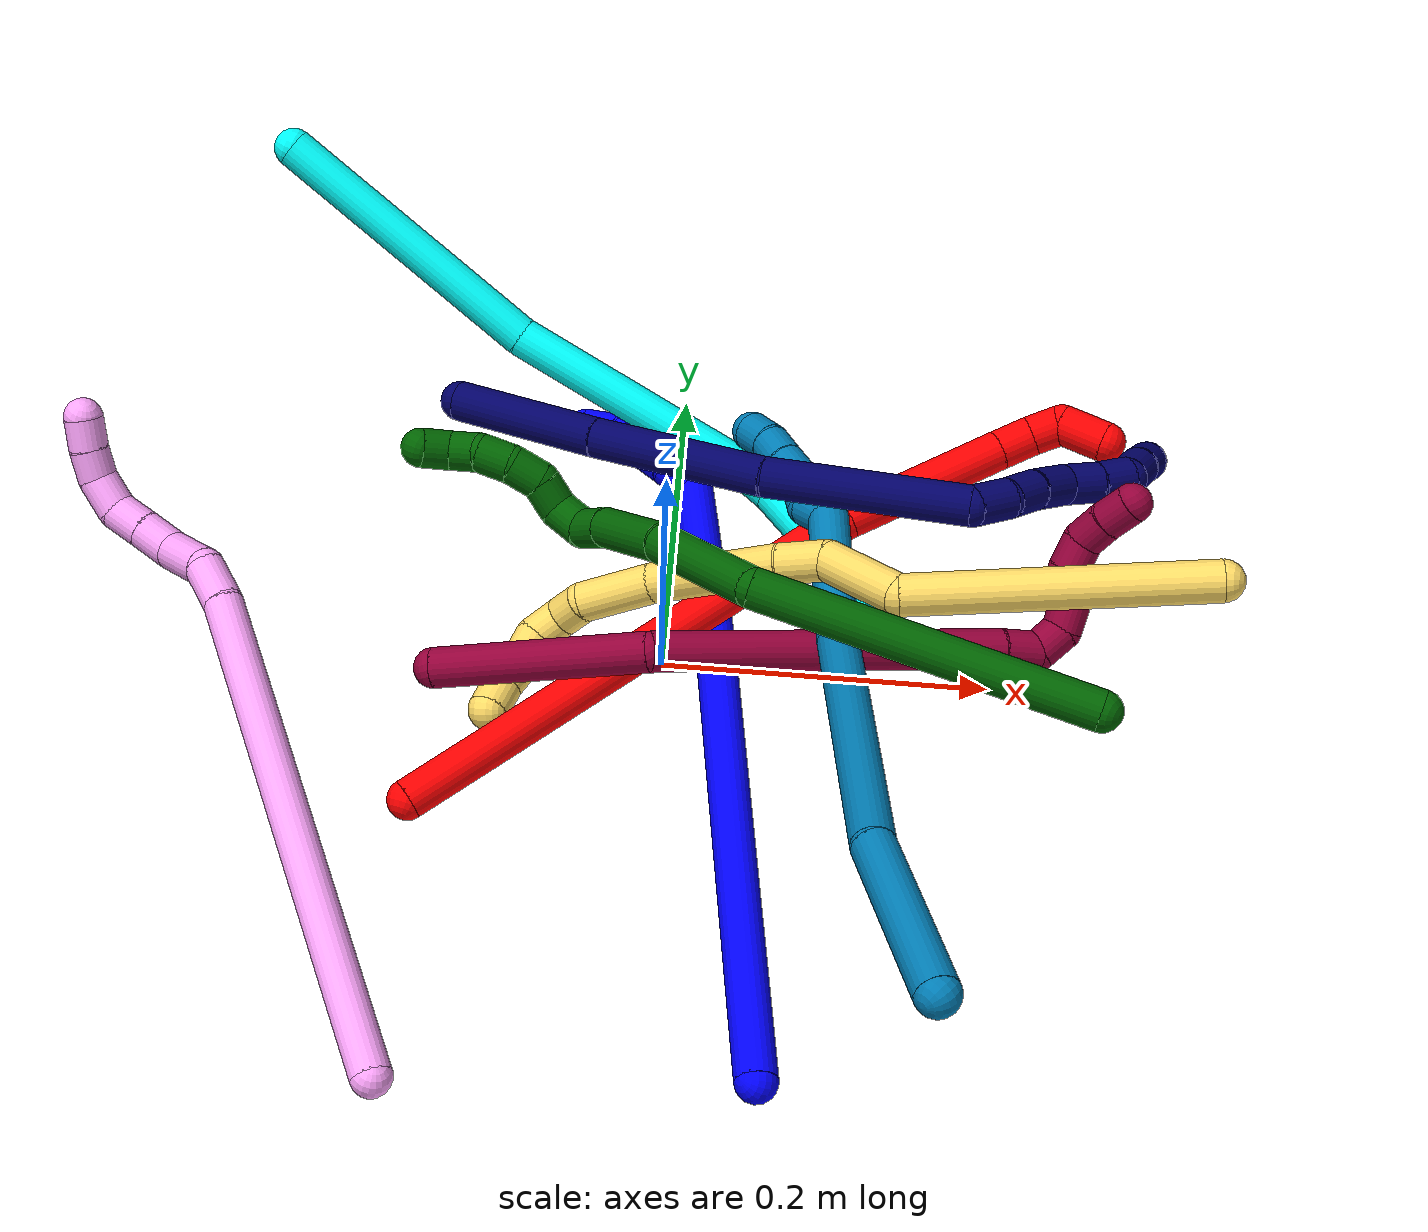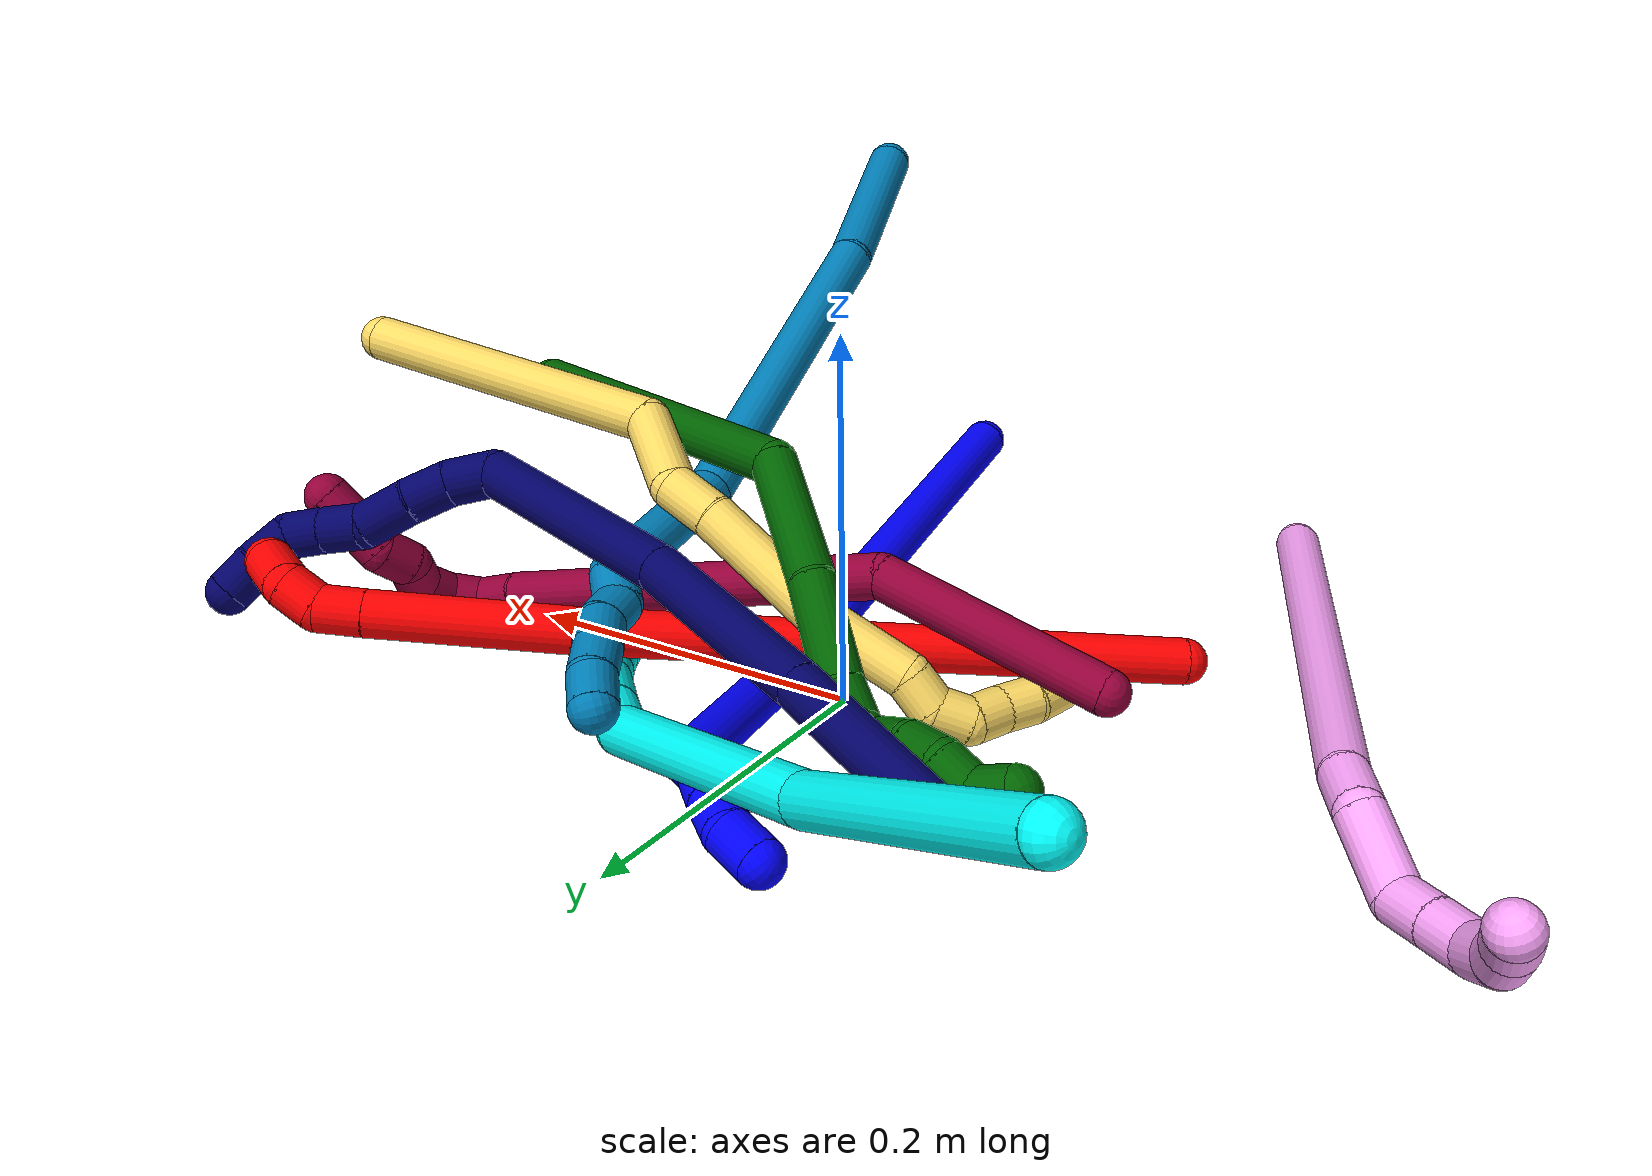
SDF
<sdf version="1.7">
 <world name="default">
  <plugin name="TubeGeneratorPlugin" filename="libtube_generator_plugin.so"/>
  <model name="photoneo_s_sensor">
   <static>1</static>
   <pose>0 0 2 1.57079 1.57079 3.14159</pose>
   <link name="link">
    <inertial><mass>0.1</mass></inertial>
    <sensor name="sensor" type="depth">
     <update_rate>30</update_rate>
     <camera>
      <horizontal_fov>1.22</horizontal_fov>
      <image><width>1920</width><height>1200</height><format>B8G8R8</format></image>
      <clip><near>0.1</near><far>4</far></clip>
      <depth_camera><output>points</output></depth_camera>
     </camera>
     <plugin name="camera_plugin" filename="libgazebo_ros_depth_camera.so">
      <baseline>0.2</baseline>
      <alwaysOn>1</alwaysOn>
      <updateRate>0.0</updateRate>
      <cameraName>camera_ir</cameraName>
      <imageTopicName>/camera/color/image_raw</imageTopicName>
      <cameraInfoTopicName>/camera/color/camera_info</cameraInfoTopicName>
      <depthImageTopicName>/camera/depth/image_raw</depthImageTopicName>
      <depthImageCameraInfoTopicName>/camera/depth/camera_info</depthImageCameraInfoTopicName>
      <pointCloudTopicName>/camera/depth/points</pointCloudTopicName>
      <frameName>fr_optical</frameName>
      <pointCloudCutoff>0.1</pointCloudCutoff>
      <pointCloudCutoffMax>2.0</pointCloudCutoffMax>
      <distortionK1>0</distortionK1>
      <distortionK2>0</distortionK2>
      <distortionK3>0</distortionK3>
      <distortionT1>0</distortionT1>
      <distortionT2>0</distortionT2>
      <CxPrime>0</CxPrime>
      <Cx>0</Cx>
      <Cy>0</Cy>
      <focalLength>0</focalLength>
      <hackBaseline>0</hackBaseline>
     </plugin>
    </sensor>
   </link>
  </model>
  <gravity>0 0 -9.8</gravity>
  <magnetic_field>6e-06 2.3e-05 -4.2e-05</magnetic_field>
  <atmosphere type="adiabatic"/>
  <physics name="default_physics" default="0" type="ode">
   <max_step_size>0.003</max_step_size>
   <real_time_factor>1</real_time_factor>
   <real_time_update_rate>1000</real_time_update_rate>
   <max_contacts>10000</max_contacts>
   <ode>
    <solver>
     <type>quick</type>
     <iters>100</iters>
     <sor>1.3</sor>
     <use_dynamic_moi_rescaling>0</use_dynamic_moi_rescaling>
    </solver>
    <constraints>
     <contact_max_correcting_vel>0</contact_max_correcting_vel>
     <contact_surface_layer>0.001</contact_surface_layer>
     <cfm>0</cfm>
     <erp>0.2</erp>
    </constraints>
   </ode>
  </physics>
  <scene><ambient>0.4 0.4 0.4 1</ambient><background>0.7 0.7 0.7 1</background><shadows>0</shadows></scene>
  <audio><device>default</device></audio>
  <spherical_coordinates>
   <surface_model>EARTH_WGS84</surface_model>
   <latitude_deg>0</latitude_deg>
   <longitude_deg>0</longitude_deg>
   <elevation>0</elevation>
   <heading_deg>0</heading_deg>
  </spherical_coordinates>
  <model name="bin">
   <static>1</static>
   <link name="bottom">
    <collision name="collision-bottom">
     <pose>0 0 -0.01 0 -0 0</pose>
     <geometry><box><size>0.8 0.6 0.02</size></box></geometry>
     <surface>
      <friction><ode><mu>100</mu><mu2>100</mu2></ode></friction>
      <contact><collide_bitmask>65535</collide_bitmask></contact>
     </surface>
    </collision>
   </link>
   <link name="west_wall">
    <collision name="collision-west_wall">
     <pose>-0.41 0 0.1 0 -0 0</pose>
     <geometry><box><size>0.02 0.6 0.2</size></box></geometry>
     <surface>
      <friction><ode><mu>100</mu><mu2>100</mu2></ode></friction>
      <contact><collide_bitmask>65535</collide_bitmask></contact>
     </surface>
    </collision>
   </link>
   <link name="east_wall">
    <collision name="collision-east_wall">
     <pose>0.41 0 0.1 0 -0 0</pose>
     <geometry><box><size>0.02 0.6 0.2</size></box></geometry>
     <surface>
      <friction><ode><mu>100</mu><mu2>100</mu2></ode></friction>
      <contact><collide_bitmask>65535</collide_bitmask></contact>
     </surface>
    </collision>
   </link>
   <link name="south_wall">
    <collision name="collision-south_wall">
     <pose>0 -0.31 0.1 0 -0 0</pose>
     <geometry><box><size>0.8 0.02 0.2</size></box></geometry>
     <surface>
      <friction><ode><mu>100</mu><mu2>100</mu2></ode></friction>
      <contact><collide_bitmask>65535</collide_bitmask></contact>
     </surface>
    </collision>
   </link>
   <link name="north_wall">
    <collision name="collision-north_wall">
     <pose>0 0.31 0.1 0 -0 0</pose>
     <geometry><box><size>0.8 0.02 0.2</size></box></geometry>
     <surface>
      <friction><ode><mu>100</mu><mu2>100</mu2></ode></friction>
      <contact><collide_bitmask>65535</collide_bitmask></contact>
     </surface>
    </collision>
   </link>
  </model>
  <model name="1">
   <static>0</static>
   <link name="1">
    <collision name="collision-cylinder-e_1_1_4">
     <pose>-0.019028 0.145286 -0.026434 -1.75077 -0.128146 0.153474</pose>
     <geometry><cylinder><radius>0.0125</radius><length>0.297784</length></cylinder></geometry>
     <surface>
      <friction><ode><mu>1.16</mu><mu2>1.16</mu2><slip1>0</slip1><slip2>0</slip2></ode></friction>
      <contact><ode><kp>1e+06</kp><kd>1</kd><max_vel>0</max_vel><min_depth>0.001</min_depth></ode></contact>
     </surface>
    </collision>
    <visual name="visual-cylinder-e_1_1_4">
     <pose>-0.019028 0.145286 -0.026434 -1.75077 -0.128146 0.153474</pose>
     <geometry><cylinder><radius>0.0125</radius><length>0.297784</length></cylinder></geometry>
     <material><ambient>0 0 1 1</ambient></material>
    </visual>
    <collision name="collision-cylinder-e_2_4_5">
     <pose>-0.039605 0.347386 -0.054067 -1.59189 -0.027253 0.027833</pose>
     <geometry><cylinder><radius>0.0125</radius><length>0.113697</length></cylinder></geometry>
     <surface>
      <friction><ode><mu>1.16</mu><mu2>1.16</mu2><slip1>0</slip1><slip2>0</slip2></ode></friction>
      <contact><ode><kp>1e+06</kp><kd>1</kd><max_vel>0</max_vel><min_depth>0.001</min_depth></ode></contact>
     </surface>
    </collision>
    <visual name="visual-cylinder-e_2_4_5">
     <pose>-0.039605 0.347386 -0.054067 -1.59189 -0.027253 0.027833</pose>
     <geometry><cylinder><radius>0.0125</radius><length>0.113697</length></cylinder></geometry>
     <material><ambient>0 0 1 1</ambient></material>
    </visual>
    <collision name="collision-cylinder-e_3_5_6">
     <pose>-0.045358 0.411917 -0.048949 -0.884856 -0.39901 0.190997</pose>
     <geometry><cylinder><radius>0.0125</radius><length>0.021643</length></cylinder></geometry>
     <surface>
      <friction><ode><mu>1.16</mu><mu2>1.16</mu2><slip1>0</slip1><slip2>0</slip2></ode></friction>
      <contact><ode><kp>1e+06</kp><kd>1</kd><max_vel>0</max_vel><min_depth>0.001</min_depth></ode></contact>
     </surface>
    </collision>
    <visual name="visual-cylinder-e_3_5_6">
     <pose>-0.045358 0.411917 -0.048949 -0.884856 -0.39901 0.190997</pose>
     <geometry><cylinder><radius>0.0125</radius><length>0.021643</length></cylinder></geometry>
     <material><ambient>0 0 1 1</ambient></material>
    </visual>
    <collision name="collision-cylinder-e_4_6_7">
     <pose>-0.055784 0.427985 -0.03918 -1.17877 -0.602952 0.410007</pose>
     <geometry><cylinder><radius>0.0125</radius><length>0.021944</length></cylinder></geometry>
     <surface>
      <friction><ode><mu>1.16</mu><mu2>1.16</mu2><slip1>0</slip1><slip2>0</slip2></ode></friction>
      <contact><ode><kp>1e+06</kp><kd>1</kd><max_vel>0</max_vel><min_depth>0.001</min_depth></ode></contact>
     </surface>
    </collision>
    <visual name="visual-cylinder-e_4_6_7">
     <pose>-0.055784 0.427985 -0.03918 -1.17877 -0.602952 0.410007</pose>
     <geometry><cylinder><radius>0.0125</radius><length>0.021944</length></cylinder></geometry>
     <material><ambient>0 0 1 1</ambient></material>
    </visual>
    <collision name="collision-cylinder-e_5_7_8">
     <pose>-0.068544 0.444337 -0.031782 -1.11263 -0.632467 0.401461</pose>
     <geometry><cylinder><radius>0.0125</radius><length>0.02212</length></cylinder></geometry>
     <surface>
      <friction><ode><mu>1.16</mu><mu2>1.16</mu2><slip1>0</slip1><slip2>0</slip2></ode></friction>
      <contact><ode><kp>1e+06</kp><kd>1</kd><max_vel>0</max_vel><min_depth>0.001</min_depth></ode></contact>
     </surface>
    </collision>
    <visual name="visual-cylinder-e_5_7_8">
     <pose>-0.068544 0.444337 -0.031782 -1.11263 -0.632467 0.401461</pose>
     <geometry><cylinder><radius>0.0125</radius><length>0.02212</length></cylinder></geometry>
     <material><ambient>0 0 1 1</ambient></material>
    </visual>
    <collision name="collision-cylinder-e_6_8_2">
     <pose>-0.084038 0.457009 -0.022537 -0.722556 -0.902965 0.36242</pose>
     <geometry><cylinder><radius>0.0125</radius><length>0.022812</length></cylinder></geometry>
     <surface>
      <friction><ode><mu>1.16</mu><mu2>1.16</mu2><slip1>0</slip1><slip2>0</slip2></ode></friction>
      <contact><ode><kp>1e+06</kp><kd>1</kd><max_vel>0</max_vel><min_depth>0.001</min_depth></ode></contact>
     </surface>
    </collision>
    <visual name="visual-cylinder-e_6_8_2">
     <pose>-0.084038 0.457009 -0.022537 -0.722556 -0.902965 0.36242</pose>
     <geometry><cylinder><radius>0.0125</radius><length>0.022812</length></cylinder></geometry>
     <material><ambient>0 0 1 1</ambient></material>
    </visual>
    <collision name="collision-sphere-2">
     <pose>-0.092994 0.46168 -0.017239 0 -0 0</pose>
     <geometry><sphere><radius>0.0125</radius></sphere></geometry>
     <surface>
      <friction><ode><mu>1.16</mu><mu2>1.16</mu2><slip1>0</slip1><slip2>0</slip2></ode></friction>
      <contact><ode><kp>1e+06</kp><kd>1</kd><max_vel>0</max_vel><min_depth>0.001</min_depth></ode></contact>
     </surface>
    </collision>
    <visual name="visual-sphere-2">
     <pose>-0.092994 0.46168 -0.017239 0 -0 0</pose>
     <geometry><sphere><radius>0.0125</radius></sphere></geometry>
     <material><ambient>0 0 1 1</ambient></material>
    </visual>
    <collision name="collision-sphere-4">
     <pose>-0.038056 0.290571 -0.052868 0 -0 0</pose>
     <geometry><sphere><radius>0.0125</radius></sphere></geometry>
     <surface>
      <friction><ode><mu>1.16</mu><mu2>1.16</mu2><slip1>0</slip1><slip2>0</slip2></ode></friction>
      <contact><ode><kp>1e+06</kp><kd>1</kd><max_vel>0</max_vel><min_depth>0.001</min_depth></ode></contact>
     </surface>
    </collision>
    <visual name="visual-sphere-4">
     <pose>-0.038056 0.290571 -0.052868 0 -0 0</pose>
     <geometry><sphere><radius>0.0125</radius></sphere></geometry>
     <material><ambient>0 0 1 1</ambient></material>
    </visual>
    <collision name="collision-sphere-1">
     <geometry><sphere><radius>0.0125</radius></sphere></geometry>
     <surface>
      <friction><ode><mu>1.16</mu><mu2>1.16</mu2><slip1>0</slip1><slip2>0</slip2></ode></friction>
      <contact><ode><kp>1e+06</kp><kd>1</kd><max_vel>0</max_vel><min_depth>0.001</min_depth></ode></contact>
     </surface>
    </collision>
    <visual name="visual-sphere-1">
     <geometry><sphere><radius>0.0125</radius></sphere></geometry>
     <material><ambient>0 0 1 1</ambient></material>
    </visual>
    <collision name="collision-sphere-8">
     <pose>-0.075082 0.452338 -0.027836 0 -0 0</pose>
     <geometry><sphere><radius>0.0125</radius></sphere></geometry>
     <surface>
      <friction><ode><mu>1.16</mu><mu2>1.16</mu2><slip1>0</slip1><slip2>0</slip2></ode></friction>
      <contact><ode><kp>1e+06</kp><kd>1</kd><max_vel>0</max_vel><min_depth>0.001</min_depth></ode></contact>
     </surface>
    </collision>
    <visual name="visual-sphere-8">
     <pose>-0.075082 0.452338 -0.027836 0 -0 0</pose>
     <geometry><sphere><radius>0.0125</radius></sphere></geometry>
     <material><ambient>0 0 1 1</ambient></material>
    </visual>
    <collision name="collision-sphere-5">
     <pose>-0.041154 0.404201 -0.055265 0 -0 0</pose>
     <geometry><sphere><radius>0.0125</radius></sphere></geometry>
     <surface>
      <friction><ode><mu>1.16</mu><mu2>1.16</mu2><slip1>0</slip1><slip2>0</slip2></ode></friction>
      <contact><ode><kp>1e+06</kp><kd>1</kd><max_vel>0</max_vel><min_depth>0.001</min_depth></ode></contact>
     </surface>
    </collision>
    <visual name="visual-sphere-5">
     <pose>-0.041154 0.404201 -0.055265 0 -0 0</pose>
     <geometry><sphere><radius>0.0125</radius></sphere></geometry>
     <material><ambient>0 0 1 1</ambient></material>
    </visual>
    <collision name="collision-sphere-6">
     <pose>-0.049562 0.419633 -0.042633 0 -0 0</pose>
     <geometry><sphere><radius>0.0125</radius></sphere></geometry>
     <surface>
      <friction><ode><mu>1.16</mu><mu2>1.16</mu2><slip1>0</slip1><slip2>0</slip2></ode></friction>
      <contact><ode><kp>1e+06</kp><kd>1</kd><max_vel>0</max_vel><min_depth>0.001</min_depth></ode></contact>
     </surface>
    </collision>
    <visual name="visual-sphere-6">
     <pose>-0.049562 0.419633 -0.042633 0 -0 0</pose>
     <geometry><sphere><radius>0.0125</radius></sphere></geometry>
     <material><ambient>0 0 1 1</ambient></material>
    </visual>
    <collision name="collision-sphere-7">
     <pose>-0.062006 0.436337 -0.035727 0 -0 0</pose>
     <geometry><sphere><radius>0.0125</radius></sphere></geometry>
     <surface>
      <friction><ode><mu>1.16</mu><mu2>1.16</mu2><slip1>0</slip1><slip2>0</slip2></ode></friction>
      <contact><ode><kp>1e+06</kp><kd>1</kd><max_vel>0</max_vel><min_depth>0.001</min_depth></ode></contact>
     </surface>
    </collision>
    <visual name="visual-sphere-7">
     <pose>-0.062006 0.436337 -0.035727 0 -0 0</pose>
     <geometry><sphere><radius>0.0125</radius></sphere></geometry>
     <material><ambient>0 0 1 1</ambient></material>
    </visual>
    <inertial>
     <pose>-0.031616 0.242643 -0.03431 0 -0 0</pose>
     <mass>0.5</mass>
     <inertia><ixx>0.002634</ixx><ixy>0</ixy><ixz>0</ixz><iyy>3e-05</iyy><iyz>0</iyz><izz>-0.002001</izz></inertia>
    </inertial>
   </link>
   <pose>0.073627 -0.283161 0.042712 0.167465 -0.858705 0.066854</pose>
  </model>
  <model name="2">
   <static>0</static>
   <link name="2">
    <collision name="collision-cylinder-e_1_1_4">
     <pose>0.093615 0.027585 0.126773 -0.214255 0.62505 -0.069467</pose>
     <geometry><cylinder><radius>0.0125</radius><length>0.319976</length></cylinder></geometry>
     <surface>
      <friction><ode><mu>1.16</mu><mu2>1.16</mu2><slip1>0</slip1><slip2>0</slip2></ode></friction>
      <contact><ode><kp>1e+06</kp><kd>1</kd><max_vel>0</max_vel><min_depth>0.001</min_depth></ode></contact>
     </surface>
    </collision>
    <visual name="visual-cylinder-e_1_1_4">
     <pose>0.093615 0.027585 0.126773 -0.214255 0.62505 -0.069467</pose>
     <geometry><cylinder><radius>0.0125</radius><length>0.319976</length></cylinder></geometry>
     <material><ambient>1 0 0 1</ambient></material>
    </visual>
    <collision name="collision-cylinder-e_2_4_5">
     <pose>0.223835 0.065012 0.290709 -0.258869 0.760906 -0.10402</pose>
     <geometry><cylinder><radius>0.0125</radius><length>0.106167</length></cylinder></geometry>
     <surface>
      <friction><ode><mu>1.16</mu><mu2>1.16</mu2><slip1>0</slip1><slip2>0</slip2></ode></friction>
      <contact><ode><kp>1e+06</kp><kd>1</kd><max_vel>0</max_vel><min_depth>0.001</min_depth></ode></contact>
     </surface>
    </collision>
    <visual name="visual-cylinder-e_2_4_5">
     <pose>0.223835 0.065012 0.290709 -0.258869 0.760906 -0.10402</pose>
     <geometry><cylinder><radius>0.0125</radius><length>0.106167</length></cylinder></geometry>
     <material><ambient>1 0 0 1</ambient></material>
    </visual>
    <collision name="collision-cylinder-e_3_5_6">
     <pose>0.269037 0.076873 0.336244 -0.236797 0.784462 -0.098336</pose>
     <geometry><cylinder><radius>0.0125</radius><length>0.024336</length></cylinder></geometry>
     <surface>
      <friction><ode><mu>1.16</mu><mu2>1.16</mu2><slip1>0</slip1><slip2>0</slip2></ode></friction>
      <contact><ode><kp>1e+06</kp><kd>1</kd><max_vel>0</max_vel><min_depth>0.001</min_depth></ode></contact>
     </surface>
    </collision>
    <visual name="visual-cylinder-e_3_5_6">
     <pose>0.269037 0.076873 0.336244 -0.236797 0.784462 -0.098336</pose>
     <geometry><cylinder><radius>0.0125</radius><length>0.024336</length></cylinder></geometry>
     <material><ambient>1 0 0 1</ambient></material>
    </visual>
    <collision name="collision-cylinder-e_4_6_7">
     <pose>0.285978 0.076029 0.349469 0.533204 0.976835 0.288219</pose>
     <geometry><cylinder><radius>0.0125</radius><length>0.020141</length></cylinder></geometry>
     <surface>
      <friction><ode><mu>1.16</mu><mu2>1.16</mu2><slip1>0</slip1><slip2>0</slip2></ode></friction>
      <contact><ode><kp>1e+06</kp><kd>1</kd><max_vel>0</max_vel><min_depth>0.001</min_depth></ode></contact>
     </surface>
    </collision>
    <visual name="visual-cylinder-e_4_6_7">
     <pose>0.285978 0.076029 0.349469 0.533204 0.976835 0.288219</pose>
     <geometry><cylinder><radius>0.0125</radius><length>0.020141</length></cylinder></geometry>
     <material><ambient>1 0 0 1</ambient></material>
    </visual>
    <collision name="collision-cylinder-e_5_7_2">
     <pose>0.308778 0.072412 0.351808 2.85108 1.39116 2.79463</pose>
     <geometry><cylinder><radius>0.0125</radius><length>0.02938</length></cylinder></geometry>
     <surface>
      <friction><ode><mu>1.16</mu><mu2>1.16</mu2><slip1>0</slip1><slip2>0</slip2></ode></friction>
      <contact><ode><kp>1e+06</kp><kd>1</kd><max_vel>0</max_vel><min_depth>0.001</min_depth></ode></contact>
     </surface>
    </collision>
    <visual name="visual-cylinder-e_5_7_2">
     <pose>0.308778 0.072412 0.351808 2.85108 1.39116 2.79463</pose>
     <geometry><cylinder><radius>0.0125</radius><length>0.02938</length></cylinder></geometry>
     <material><ambient>1 0 0 1</ambient></material>
    </visual>
    <collision name="collision-sphere-2">
     <pose>0.323231 0.07166 0.349293 0 -0 0</pose>
     <geometry><sphere><radius>0.0125</radius></sphere></geometry>
     <surface>
      <friction><ode><mu>1.16</mu><mu2>1.16</mu2><slip1>0</slip1><slip2>0</slip2></ode></friction>
      <contact><ode><kp>1e+06</kp><kd>1</kd><max_vel>0</max_vel><min_depth>0.001</min_depth></ode></contact>
     </surface>
    </collision>
    <visual name="visual-sphere-2">
     <pose>0.323231 0.07166 0.349293 0 -0 0</pose>
     <geometry><sphere><radius>0.0125</radius></sphere></geometry>
     <material><ambient>1 0 0 1</ambient></material>
    </visual>
    <collision name="collision-sphere-7">
     <pose>0.294324 0.073164 0.354323 0 -0 0</pose>
     <geometry><sphere><radius>0.0125</radius></sphere></geometry>
     <surface>
      <friction><ode><mu>1.16</mu><mu2>1.16</mu2><slip1>0</slip1><slip2>0</slip2></ode></friction>
      <contact><ode><kp>1e+06</kp><kd>1</kd><max_vel>0</max_vel><min_depth>0.001</min_depth></ode></contact>
     </surface>
    </collision>
    <visual name="visual-sphere-7">
     <pose>0.294324 0.073164 0.354323 0 -0 0</pose>
     <geometry><sphere><radius>0.0125</radius></sphere></geometry>
     <material><ambient>1 0 0 1</ambient></material>
    </visual>
    <collision name="collision-sphere-6">
     <pose>0.277633 0.078893 0.344616 0 -0 0</pose>
     <geometry><sphere><radius>0.0125</radius></sphere></geometry>
     <surface>
      <friction><ode><mu>1.16</mu><mu2>1.16</mu2><slip1>0</slip1><slip2>0</slip2></ode></friction>
      <contact><ode><kp>1e+06</kp><kd>1</kd><max_vel>0</max_vel><min_depth>0.001</min_depth></ode></contact>
     </surface>
    </collision>
    <visual name="visual-sphere-6">
     <pose>0.277633 0.078893 0.344616 0 -0 0</pose>
     <geometry><sphere><radius>0.0125</radius></sphere></geometry>
     <material><ambient>1 0 0 1</ambient></material>
    </visual>
    <collision name="collision-sphere-5">
     <pose>0.260441 0.074853 0.327872 0 -0 0</pose>
     <geometry><sphere><radius>0.0125</radius></sphere></geometry>
     <surface>
      <friction><ode><mu>1.16</mu><mu2>1.16</mu2><slip1>0</slip1><slip2>0</slip2></ode></friction>
      <contact><ode><kp>1e+06</kp><kd>1</kd><max_vel>0</max_vel><min_depth>0.001</min_depth></ode></contact>
     </surface>
    </collision>
    <visual name="visual-sphere-5">
     <pose>0.260441 0.074853 0.327872 0 -0 0</pose>
     <geometry><sphere><radius>0.0125</radius></sphere></geometry>
     <material><ambient>1 0 0 1</ambient></material>
    </visual>
    <collision name="collision-sphere-1">
     <geometry><sphere><radius>0.0125</radius></sphere></geometry>
     <surface>
      <friction><ode><mu>1.16</mu><mu2>1.16</mu2><slip1>0</slip1><slip2>0</slip2></ode></friction>
      <contact><ode><kp>1e+06</kp><kd>1</kd><max_vel>0</max_vel><min_depth>0.001</min_depth></ode></contact>
     </surface>
    </collision>
    <visual name="visual-sphere-1">
     <geometry><sphere><radius>0.0125</radius></sphere></geometry>
     <material><ambient>1 0 0 1</ambient></material>
    </visual>
    <collision name="collision-sphere-4">
     <pose>0.18723 0.05517 0.253547 0 -0 0</pose>
     <geometry><sphere><radius>0.0125</radius></sphere></geometry>
     <surface>
      <friction><ode><mu>1.16</mu><mu2>1.16</mu2><slip1>0</slip1><slip2>0</slip2></ode></friction>
      <contact><ode><kp>1e+06</kp><kd>1</kd><max_vel>0</max_vel><min_depth>0.001</min_depth></ode></contact>
     </surface>
    </collision>
    <visual name="visual-sphere-4">
     <pose>0.18723 0.05517 0.253547 0 -0 0</pose>
     <geometry><sphere><radius>0.0125</radius></sphere></geometry>
     <material><ambient>1 0 0 1</ambient></material>
    </visual>
    <inertial>
     <pose>0.150195 0.042516 0.193971 0 -0 0</pose>
     <mass>0.5</mass>
     <inertia>
      <ixx>0.002159</ixx>
      <ixy>0</ixy>
      <ixz>0</ixz>
      <iyy>0.002649</iyy>
      <iyz>0</iyz>
      <izz>-0.002147</izz>
     </inertia>
    </inertial>
   </link>
   <pose>-0.142287 -0.112743 0.011897 -1.27674 -0.086028 -0.278756</pose>
  </model>
  <model name="3">
   <static>0</static>
   <link name="3">
    <collision name="collision-cylinder-e_1_1_4">
     <pose>-0.000251 -0.025427 -0.089431 2.86458 -0.002703 -0.019392</pose>
     <geometry><cylinder><radius>0.0125</radius><length>0.185951</length></cylinder></geometry>
     <surface>
      <friction><ode><mu>1.16</mu><mu2>1.16</mu2><slip1>0</slip1><slip2>0</slip2></ode></friction>
      <contact><ode><kp>1e+06</kp><kd>1</kd><max_vel>0</max_vel><min_depth>0.001</min_depth></ode></contact>
     </surface>
    </collision>
    <visual name="visual-cylinder-e_1_1_4">
     <pose>-0.000251 -0.025427 -0.089431 2.86458 -0.002703 -0.019392</pose>
     <geometry><cylinder><radius>0.0125</radius><length>0.185951</length></cylinder></geometry>
     <material><ambient>0.003922 1 0.996078 1</ambient></material>
    </visual>
    <collision name="collision-cylinder-e_2_4_5">
     <pose>0.005912 -0.059751 -0.261089 3.0338 0.0774 1.24505</pose>
     <geometry><cylinder><radius>0.0125</radius><length>0.165912</length></cylinder></geometry>
     <surface>
      <friction><ode><mu>1.16</mu><mu2>1.16</mu2><slip1>0</slip1><slip2>0</slip2></ode></friction>
      <contact><ode><kp>1e+06</kp><kd>1</kd><max_vel>0</max_vel><min_depth>0.001</min_depth></ode></contact>
     </surface>
    </collision>
    <visual name="visual-cylinder-e_2_4_5">
     <pose>0.005912 -0.059751 -0.261089 3.0338 0.0774 1.24505</pose>
     <geometry><cylinder><radius>0.0125</radius><length>0.165912</length></cylinder></geometry>
     <material><ambient>0.003922 1 0.996078 1</ambient></material>
    </visual>
    <collision name="collision-cylinder-e_3_5_6">
     <pose>0.017609 -0.070813 -0.353676 2.93564 0.462976 2.31521</pose>
     <geometry><cylinder><radius>0.0125</radius><length>0.023656</length></cylinder></geometry>
     <surface>
      <friction><ode><mu>1.16</mu><mu2>1.16</mu2><slip1>0</slip1><slip2>0</slip2></ode></friction>
      <contact><ode><kp>1e+06</kp><kd>1</kd><max_vel>0</max_vel><min_depth>0.001</min_depth></ode></contact>
     </surface>
    </collision>
    <visual name="visual-cylinder-e_3_5_6">
     <pose>0.017609 -0.070813 -0.353676 2.93564 0.462976 2.31521</pose>
     <geometry><cylinder><radius>0.0125</radius><length>0.023656</length></cylinder></geometry>
     <material><ambient>0.003922 1 0.996078 1</ambient></material>
    </visual>
    <collision name="collision-cylinder-e_4_6_7">
     <pose>0.030888 -0.079716 -0.381707 2.77729 0.400032 1.66652</pose>
     <geometry><cylinder><radius>0.0125</radius><length>0.041069</length></cylinder></geometry>
     <surface>
      <friction><ode><mu>1.16</mu><mu2>1.16</mu2><slip1>0</slip1><slip2>0</slip2></ode></friction>
      <contact><ode><kp>1e+06</kp><kd>1</kd><max_vel>0</max_vel><min_depth>0.001</min_depth></ode></contact>
     </surface>
    </collision>
    <visual name="visual-cylinder-e_4_6_7">
     <pose>0.030888 -0.079716 -0.381707 2.77729 0.400032 1.66652</pose>
     <geometry><cylinder><radius>0.0125</radius><length>0.041069</length></cylinder></geometry>
     <material><ambient>0.003922 1 0.996078 1</ambient></material>
    </visual>
    <collision name="collision-cylinder-e_5_7_8">
     <pose>0.042732 -0.091796 -0.408161 2.59523 0.358098 1.14705</pose>
     <geometry><cylinder><radius>0.0125</radius><length>0.021949</length></cylinder></geometry>
     <surface>
      <friction><ode><mu>1.16</mu><mu2>1.16</mu2><slip1>0</slip1><slip2>0</slip2></ode></friction>
      <contact><ode><kp>1e+06</kp><kd>1</kd><max_vel>0</max_vel><min_depth>0.001</min_depth></ode></contact>
     </surface>
    </collision>
    <visual name="visual-cylinder-e_5_7_8">
     <pose>0.042732 -0.091796 -0.408161 2.59523 0.358098 1.14705</pose>
     <geometry><cylinder><radius>0.0125</radius><length>0.021949</length></cylinder></geometry>
     <material><ambient>0.003922 1 0.996078 1</ambient></material>
    </visual>
    <collision name="collision-cylinder-e_6_8_9">
     <pose>0.051042 -0.101947 -0.424779 2.59093 0.451919 1.36612</pose>
     <geometry><cylinder><radius>0.0125</radius><length>0.020442</length></cylinder></geometry>
     <surface>
      <friction><ode><mu>1.16</mu><mu2>1.16</mu2><slip1>0</slip1><slip2>0</slip2></ode></friction>
      <contact><ode><kp>1e+06</kp><kd>1</kd><max_vel>0</max_vel><min_depth>0.001</min_depth></ode></contact>
     </surface>
    </collision>
    <visual name="visual-cylinder-e_6_8_9">
     <pose>0.051042 -0.101947 -0.424779 2.59093 0.451919 1.36612</pose>
     <geometry><cylinder><radius>0.0125</radius><length>0.020442</length></cylinder></geometry>
     <material><ambient>0.003922 1 0.996078 1</ambient></material>
    </visual>
    <collision name="collision-cylinder-e_7_9_10">
     <pose>0.059876 -0.112036 -0.440329 2.54165 0.437384 1.24611</pose>
     <geometry><cylinder><radius>0.0125</radius><length>0.020637</length></cylinder></geometry>
     <surface>
      <friction><ode><mu>1.16</mu><mu2>1.16</mu2><slip1>0</slip1><slip2>0</slip2></ode></friction>
      <contact><ode><kp>1e+06</kp><kd>1</kd><max_vel>0</max_vel><min_depth>0.001</min_depth></ode></contact>
     </surface>
    </collision>
    <visual name="visual-cylinder-e_7_9_10">
     <pose>0.059876 -0.112036 -0.440329 2.54165 0.437384 1.24611</pose>
     <geometry><cylinder><radius>0.0125</radius><length>0.020637</length></cylinder></geometry>
     <material><ambient>0.003922 1 0.996078 1</ambient></material>
    </visual>
    <collision name="collision-cylinder-e_8_10_2">
     <pose>0.069027 -0.117448 -0.457044 3.12661 0.488211 3.08146</pose>
     <geometry><cylinder><radius>0.0125</radius><length>0.020384</length></cylinder></geometry>
     <surface>
      <friction><ode><mu>1.16</mu><mu2>1.16</mu2><slip1>0</slip1><slip2>0</slip2></ode></friction>
      <contact><ode><kp>1e+06</kp><kd>1</kd><max_vel>0</max_vel><min_depth>0.001</min_depth></ode></contact>
     </surface>
    </collision>
    <visual name="visual-cylinder-e_8_10_2">
     <pose>0.069027 -0.117448 -0.457044 3.12661 0.488211 3.08146</pose>
     <geometry><cylinder><radius>0.0125</radius><length>0.020384</length></cylinder></geometry>
     <material><ambient>0.003922 1 0.996078 1</ambient></material>
    </visual>
    <collision name="collision-sphere-2">
     <pose>0.073808 -0.117583 -0.466045 0 -0 0</pose>
     <geometry><sphere><radius>0.0125</radius></sphere></geometry>
     <surface>
      <friction><ode><mu>1.16</mu><mu2>1.16</mu2><slip1>0</slip1><slip2>0</slip2></ode></friction>
      <contact><ode><kp>1e+06</kp><kd>1</kd><max_vel>0</max_vel><min_depth>0.001</min_depth></ode></contact>
     </surface>
    </collision>
    <visual name="visual-sphere-2">
     <pose>0.073808 -0.117583 -0.466045 0 -0 0</pose>
     <geometry><sphere><radius>0.0125</radius></sphere></geometry>
     <material><ambient>0.003922 1 0.996078 1</ambient></material>
    </visual>
    <collision name="collision-sphere-10">
     <pose>0.064246 -0.117313 -0.448044 0 -0 0</pose>
     <geometry><sphere><radius>0.0125</radius></sphere></geometry>
     <surface>
      <friction><ode><mu>1.16</mu><mu2>1.16</mu2><slip1>0</slip1><slip2>0</slip2></ode></friction>
      <contact><ode><kp>1e+06</kp><kd>1</kd><max_vel>0</max_vel><min_depth>0.001</min_depth></ode></contact>
     </surface>
    </collision>
    <visual name="visual-sphere-10">
     <pose>0.064246 -0.117313 -0.448044 0 -0 0</pose>
     <geometry><sphere><radius>0.0125</radius></sphere></geometry>
     <material><ambient>0.003922 1 0.996078 1</ambient></material>
    </visual>
    <collision name="collision-sphere-9">
     <pose>0.055505 -0.106758 -0.432614 0 -0 0</pose>
     <geometry><sphere><radius>0.0125</radius></sphere></geometry>
     <surface>
      <friction><ode><mu>1.16</mu><mu2>1.16</mu2><slip1>0</slip1><slip2>0</slip2></ode></friction>
      <contact><ode><kp>1e+06</kp><kd>1</kd><max_vel>0</max_vel><min_depth>0.001</min_depth></ode></contact>
     </surface>
    </collision>
    <visual name="visual-sphere-9">
     <pose>0.055505 -0.106758 -0.432614 0 -0 0</pose>
     <geometry><sphere><radius>0.0125</radius></sphere></geometry>
     <material><ambient>0.003922 1 0.996078 1</ambient></material>
    </visual>
    <collision name="collision-sphere-4">
     <pose>-0.000503 -0.050854 -0.178862 0 -0 0</pose>
     <geometry><sphere><radius>0.0125</radius></sphere></geometry>
     <surface>
      <friction><ode><mu>1.16</mu><mu2>1.16</mu2><slip1>0</slip1><slip2>0</slip2></ode></friction>
      <contact><ode><kp>1e+06</kp><kd>1</kd><max_vel>0</max_vel><min_depth>0.001</min_depth></ode></contact>
     </surface>
    </collision>
    <visual name="visual-sphere-4">
     <pose>-0.000503 -0.050854 -0.178862 0 -0 0</pose>
     <geometry><sphere><radius>0.0125</radius></sphere></geometry>
     <material><ambient>0.003922 1 0.996078 1</ambient></material>
    </visual>
    <collision name="collision-sphere-1">
     <geometry><sphere><radius>0.0125</radius></sphere></geometry>
     <surface>
      <friction><ode><mu>1.16</mu><mu2>1.16</mu2><slip1>0</slip1><slip2>0</slip2></ode></friction>
      <contact><ode><kp>1e+06</kp><kd>1</kd><max_vel>0</max_vel><min_depth>0.001</min_depth></ode></contact>
     </surface>
    </collision>
    <visual name="visual-sphere-1">
     <geometry><sphere><radius>0.0125</radius></sphere></geometry>
     <material><ambient>0.003922 1 0.996078 1</ambient></material>
    </visual>
    <collision name="collision-sphere-8">
     <pose>0.046578 -0.097136 -0.416943 0 -0 0</pose>
     <geometry><sphere><radius>0.0125</radius></sphere></geometry>
     <surface>
      <friction><ode><mu>1.16</mu><mu2>1.16</mu2><slip1>0</slip1><slip2>0</slip2></ode></friction>
      <contact><ode><kp>1e+06</kp><kd>1</kd><max_vel>0</max_vel><min_depth>0.001</min_depth></ode></contact>
     </surface>
    </collision>
    <visual name="visual-sphere-8">
     <pose>0.046578 -0.097136 -0.416943 0 -0 0</pose>
     <geometry><sphere><radius>0.0125</radius></sphere></geometry>
     <material><ambient>0.003922 1 0.996078 1</ambient></material>
    </visual>
    <collision name="collision-sphere-5">
     <pose>0.012326 -0.068649 -0.343317 0 -0 0</pose>
     <geometry><sphere><radius>0.0125</radius></sphere></geometry>
     <surface>
      <friction><ode><mu>1.16</mu><mu2>1.16</mu2><slip1>0</slip1><slip2>0</slip2></ode></friction>
      <contact><ode><kp>1e+06</kp><kd>1</kd><max_vel>0</max_vel><min_depth>0.001</min_depth></ode></contact>
     </surface>
    </collision>
    <visual name="visual-sphere-5">
     <pose>0.012326 -0.068649 -0.343317 0 -0 0</pose>
     <geometry><sphere><radius>0.0125</radius></sphere></geometry>
     <material><ambient>0.003922 1 0.996078 1</ambient></material>
    </visual>
    <collision name="collision-sphere-6">
     <pose>0.022891 -0.072978 -0.364035 0 -0 0</pose>
     <geometry><sphere><radius>0.0125</radius></sphere></geometry>
     <surface>
      <friction><ode><mu>1.16</mu><mu2>1.16</mu2><slip1>0</slip1><slip2>0</slip2></ode></friction>
      <contact><ode><kp>1e+06</kp><kd>1</kd><max_vel>0</max_vel><min_depth>0.001</min_depth></ode></contact>
     </surface>
    </collision>
    <visual name="visual-sphere-6">
     <pose>0.022891 -0.072978 -0.364035 0 -0 0</pose>
     <geometry><sphere><radius>0.0125</radius></sphere></geometry>
     <material><ambient>0.003922 1 0.996078 1</ambient></material>
    </visual>
    <collision name="collision-sphere-7">
     <pose>0.038885 -0.086455 -0.399379 0 -0 0</pose>
     <geometry><sphere><radius>0.0125</radius></sphere></geometry>
     <surface>
      <friction><ode><mu>1.16</mu><mu2>1.16</mu2><slip1>0</slip1><slip2>0</slip2></ode></friction>
      <contact><ode><kp>1e+06</kp><kd>1</kd><max_vel>0</max_vel><min_depth>0.001</min_depth></ode></contact>
     </surface>
    </collision>
    <visual name="visual-sphere-7">
     <pose>0.038885 -0.086455 -0.399379 0 -0 0</pose>
     <geometry><sphere><radius>0.0125</radius></sphere></geometry>
     <material><ambient>0.003922 1 0.996078 1</ambient></material>
    </visual>
    <inertial>
     <pose>0.014486 -0.056791 -0.240072 0 -0 0</pose>
     <mass>0.5</mass>
     <inertia>
      <ixx>0.001038</ixx>
      <ixy>0</ixy>
      <ixz>0</ixz>
      <iyy>-0.00028</iyy>
      <iyz>0</iyz>
      <izz>0.000124</izz>
     </inertia>
    </inertial>
   </link>
   <pose>-0.25679 0.27335 0.142265 1.25496 -0.79013 -1.6143</pose>
  </model>
  <model name="4">
   <static>0</static>
   <link name="4">
    <collision name="collision-cylinder-e_1_1_4">
     <pose>-0.07097 0.135585 -0.039382 -1.85347 -0.465775 0.611937</pose>
     <geometry><cylinder><radius>0.0125</radius><length>0.316044</length></cylinder></geometry>
     <surface>
      <friction><ode><mu>1.16</mu><mu2>1.16</mu2><slip1>0</slip1><slip2>0</slip2></ode></friction>
      <contact><ode><kp>1e+06</kp><kd>1</kd><max_vel>0</max_vel><min_depth>0.001</min_depth></ode></contact>
     </surface>
    </collision>
    <visual name="visual-cylinder-e_1_1_4">
     <pose>-0.07097 0.135585 -0.039382 -1.85347 -0.465775 0.611937</pose>
     <geometry><cylinder><radius>0.0125</radius><length>0.316044</length></cylinder></geometry>
     <material><ambient>1 0.65098 0.996078 1</ambient></material>
    </visual>
    <collision name="collision-cylinder-e_2_4_5">
     <pose>-0.147381 0.284941 -0.080519 -1.69759 -0.373494 0.422721</pose>
     <geometry><cylinder><radius>0.0125</radius><length>0.029822</length></cylinder></geometry>
     <surface>
      <friction><ode><mu>1.16</mu><mu2>1.16</mu2><slip1>0</slip1><slip2>0</slip2></ode></friction>
      <contact><ode><kp>1e+06</kp><kd>1</kd><max_vel>0</max_vel><min_depth>0.001</min_depth></ode></contact>
     </surface>
    </collision>
    <visual name="visual-cylinder-e_2_4_5">
     <pose>-0.147381 0.284941 -0.080519 -1.69759 -0.373494 0.422721</pose>
     <geometry><cylinder><radius>0.0125</radius><length>0.029822</length></cylinder></geometry>
     <material><ambient>1 0.65098 0.996078 1</ambient></material>
    </visual>
    <collision name="collision-cylinder-e_3_5_6">
     <pose>-0.158835 0.316917 -0.073005 -1.09986 -0.28628 0.176244</pose>
     <geometry><cylinder><radius>0.0125</radius><length>0.04259</length></cylinder></geometry>
     <surface>
      <friction><ode><mu>1.16</mu><mu2>1.16</mu2><slip1>0</slip1><slip2>0</slip2></ode></friction>
      <contact><ode><kp>1e+06</kp><kd>1</kd><max_vel>0</max_vel><min_depth>0.001</min_depth></ode></contact>
     </surface>
    </collision>
    <visual name="visual-cylinder-e_3_5_6">
     <pose>-0.158835 0.316917 -0.073005 -1.09986 -0.28628 0.176244</pose>
     <geometry><cylinder><radius>0.0125</radius><length>0.04259</length></cylinder></geometry>
     <material><ambient>1 0.65098 0.996078 1</ambient></material>
    </visual>
    <collision name="collision-cylinder-e_4_6_7">
     <pose>-0.163952 0.347324 -0.064423 -1.62695 0.073157 -0.077381</pose>
     <geometry><cylinder><radius>0.0125</radius><length>0.024509</length></cylinder></geometry>
     <surface>
      <friction><ode><mu>1.16</mu><mu2>1.16</mu2><slip1>0</slip1><slip2>0</slip2></ode></friction>
      <contact><ode><kp>1e+06</kp><kd>1</kd><max_vel>0</max_vel><min_depth>0.001</min_depth></ode></contact>
     </surface>
    </collision>
    <visual name="visual-cylinder-e_4_6_7">
     <pose>-0.163952 0.347324 -0.064423 -1.62695 0.073157 -0.077381</pose>
     <geometry><cylinder><radius>0.0125</radius><length>0.024509</length></cylinder></geometry>
     <material><ambient>1 0.65098 0.996078 1</ambient></material>
    </visual>
    <collision name="collision-cylinder-e_5_7_8">
     <pose>-0.162204 0.37095 -0.065593 -1.61315 0.074453 -0.077672</pose>
     <geometry><cylinder><radius>0.0125</radius><length>0.022929</length></cylinder></geometry>
     <surface>
      <friction><ode><mu>1.16</mu><mu2>1.16</mu2><slip1>0</slip1><slip2>0</slip2></ode></friction>
      <contact><ode><kp>1e+06</kp><kd>1</kd><max_vel>0</max_vel><min_depth>0.001</min_depth></ode></contact>
     </surface>
    </collision>
    <visual name="visual-cylinder-e_5_7_8">
     <pose>-0.162204 0.37095 -0.065593 -1.61315 0.074453 -0.077672</pose>
     <geometry><cylinder><radius>0.0125</radius><length>0.022929</length></cylinder></geometry>
     <material><ambient>1 0.65098 0.996078 1</ambient></material>
    </visual>
    <collision name="collision-cylinder-e_6_8_9">
     <pose>-0.161886 0.39273 -0.071832 -2.07792 -0.045131 0.076678</pose>
     <geometry><cylinder><radius>0.0125</radius><length>0.023722</length></cylinder></geometry>
     <surface>
      <friction><ode><mu>1.16</mu><mu2>1.16</mu2><slip1>0</slip1><slip2>0</slip2></ode></friction>
      <contact><ode><kp>1e+06</kp><kd>1</kd><max_vel>0</max_vel><min_depth>0.001</min_depth></ode></contact>
     </surface>
    </collision>
    <visual name="visual-cylinder-e_6_8_9">
     <pose>-0.161886 0.39273 -0.071832 -2.07792 -0.045131 0.076678</pose>
     <geometry><cylinder><radius>0.0125</radius><length>0.023722</length></cylinder></geometry>
     <material><ambient>1 0.65098 0.996078 1</ambient></material>
    </visual>
    <collision name="collision-cylinder-e_7_9_10">
     <pose>-0.162663 0.408808 -0.085973 -2.54299 -0.023806 0.077115</pose>
     <geometry><cylinder><radius>0.0125</radius><length>0.020309</length></cylinder></geometry>
     <surface>
      <friction><ode><mu>1.16</mu><mu2>1.16</mu2><slip1>0</slip1><slip2>0</slip2></ode></friction>
      <contact><ode><kp>1e+06</kp><kd>1</kd><max_vel>0</max_vel><min_depth>0.001</min_depth></ode></contact>
     </surface>
    </collision>
    <visual name="visual-cylinder-e_7_9_10">
     <pose>-0.162663 0.408808 -0.085973 -2.54299 -0.023806 0.077115</pose>
     <geometry><cylinder><radius>0.0125</radius><length>0.020309</length></cylinder></geometry>
     <material><ambient>1 0.65098 0.996078 1</ambient></material>
    </visual>
    <collision name="collision-cylinder-e_8_10_2">
     <pose>-0.164154 0.419531 -0.10297 -2.6153 -0.124788 0.455759</pose>
     <geometry><cylinder><radius>0.0125</radius><length>0.020075</length></cylinder></geometry>
     <surface>
      <friction><ode><mu>1.16</mu><mu2>1.16</mu2><slip1>0</slip1><slip2>0</slip2></ode></friction>
      <contact><ode><kp>1e+06</kp><kd>1</kd><max_vel>0</max_vel><min_depth>0.001</min_depth></ode></contact>
     </surface>
    </collision>
    <visual name="visual-cylinder-e_8_10_2">
     <pose>-0.164154 0.419531 -0.10297 -2.6153 -0.124788 0.455759</pose>
     <geometry><cylinder><radius>0.0125</radius><length>0.020075</length></cylinder></geometry>
     <material><ambient>1 0.65098 0.996078 1</ambient></material>
    </visual>
    <collision name="collision-sphere-2">
     <pose>-0.165403 0.424534 -0.111582 0 -0 0</pose>
     <geometry><sphere><radius>0.0125</radius></sphere></geometry>
     <surface>
      <friction><ode><mu>1.16</mu><mu2>1.16</mu2><slip1>0</slip1><slip2>0</slip2></ode></friction>
      <contact><ode><kp>1e+06</kp><kd>1</kd><max_vel>0</max_vel><min_depth>0.001</min_depth></ode></contact>
     </surface>
    </collision>
    <visual name="visual-sphere-2">
     <pose>-0.165403 0.424534 -0.111582 0 -0 0</pose>
     <geometry><sphere><radius>0.0125</radius></sphere></geometry>
     <material><ambient>1 0.65098 0.996078 1</ambient></material>
    </visual>
    <collision name="collision-sphere-10">
     <pose>-0.162905 0.414529 -0.094359 0 -0 0</pose>
     <geometry><sphere><radius>0.0125</radius></sphere></geometry>
     <surface>
      <friction><ode><mu>1.16</mu><mu2>1.16</mu2><slip1>0</slip1><slip2>0</slip2></ode></friction>
      <contact><ode><kp>1e+06</kp><kd>1</kd><max_vel>0</max_vel><min_depth>0.001</min_depth></ode></contact>
     </surface>
    </collision>
    <visual name="visual-sphere-10">
     <pose>-0.162905 0.414529 -0.094359 0 -0 0</pose>
     <geometry><sphere><radius>0.0125</radius></sphere></geometry>
     <material><ambient>1 0.65098 0.996078 1</ambient></material>
    </visual>
    <collision name="collision-sphere-9">
     <pose>-0.162421 0.403088 -0.077586 0 -0 0</pose>
     <geometry><sphere><radius>0.0125</radius></sphere></geometry>
     <surface>
      <friction><ode><mu>1.16</mu><mu2>1.16</mu2><slip1>0</slip1><slip2>0</slip2></ode></friction>
      <contact><ode><kp>1e+06</kp><kd>1</kd><max_vel>0</max_vel><min_depth>0.001</min_depth></ode></contact>
     </surface>
    </collision>
    <visual name="visual-sphere-9">
     <pose>-0.162421 0.403088 -0.077586 0 -0 0</pose>
     <geometry><sphere><radius>0.0125</radius></sphere></geometry>
     <material><ambient>1 0.65098 0.996078 1</ambient></material>
    </visual>
    <collision name="collision-sphere-4">
     <pose>-0.14194 0.27117 -0.078763 0 -0 0</pose>
     <geometry><sphere><radius>0.0125</radius></sphere></geometry>
     <surface>
      <friction><ode><mu>1.16</mu><mu2>1.16</mu2><slip1>0</slip1><slip2>0</slip2></ode></friction>
      <contact><ode><kp>1e+06</kp><kd>1</kd><max_vel>0</max_vel><min_depth>0.001</min_depth></ode></contact>
     </surface>
    </collision>
    <visual name="visual-sphere-4">
     <pose>-0.14194 0.27117 -0.078763 0 -0 0</pose>
     <geometry><sphere><radius>0.0125</radius></sphere></geometry>
     <material><ambient>1 0.65098 0.996078 1</ambient></material>
    </visual>
    <collision name="collision-sphere-1">
     <geometry><sphere><radius>0.0125</radius></sphere></geometry>
     <surface>
      <friction><ode><mu>1.16</mu><mu2>1.16</mu2><slip1>0</slip1><slip2>0</slip2></ode></friction>
      <contact><ode><kp>1e+06</kp><kd>1</kd><max_vel>0</max_vel><min_depth>0.001</min_depth></ode></contact>
     </surface>
    </collision>
    <visual name="visual-sphere-1">
     <geometry><sphere><radius>0.0125</radius></sphere></geometry>
     <material><ambient>1 0.65098 0.996078 1</ambient></material>
    </visual>
    <collision name="collision-sphere-8">
     <pose>-0.161351 0.382372 -0.066077 0 -0 0</pose>
     <geometry><sphere><radius>0.0125</radius></sphere></geometry>
     <surface>
      <friction><ode><mu>1.16</mu><mu2>1.16</mu2><slip1>0</slip1><slip2>0</slip2></ode></friction>
      <contact><ode><kp>1e+06</kp><kd>1</kd><max_vel>0</max_vel><min_depth>0.001</min_depth></ode></contact>
     </surface>
    </collision>
    <visual name="visual-sphere-8">
     <pose>-0.161351 0.382372 -0.066077 0 -0 0</pose>
     <geometry><sphere><radius>0.0125</radius></sphere></geometry>
     <material><ambient>1 0.65098 0.996078 1</ambient></material>
    </visual>
    <collision name="collision-sphere-5">
     <pose>-0.152821 0.298712 -0.082274 0 -0 0</pose>
     <geometry><sphere><radius>0.0125</radius></sphere></geometry>
     <surface>
      <friction><ode><mu>1.16</mu><mu2>1.16</mu2><slip1>0</slip1><slip2>0</slip2></ode></friction>
      <contact><ode><kp>1e+06</kp><kd>1</kd><max_vel>0</max_vel><min_depth>0.001</min_depth></ode></contact>
     </surface>
    </collision>
    <visual name="visual-sphere-5">
     <pose>-0.152821 0.298712 -0.082274 0 -0 0</pose>
     <geometry><sphere><radius>0.0125</radius></sphere></geometry>
     <material><ambient>1 0.65098 0.996078 1</ambient></material>
    </visual>
    <collision name="collision-sphere-6">
     <pose>-0.164848 0.335122 -0.063737 0 -0 0</pose>
     <geometry><sphere><radius>0.0125</radius></sphere></geometry>
     <surface>
      <friction><ode><mu>1.16</mu><mu2>1.16</mu2><slip1>0</slip1><slip2>0</slip2></ode></friction>
      <contact><ode><kp>1e+06</kp><kd>1</kd><max_vel>0</max_vel><min_depth>0.001</min_depth></ode></contact>
     </surface>
    </collision>
    <visual name="visual-sphere-6">
     <pose>-0.164848 0.335122 -0.063737 0 -0 0</pose>
     <geometry><sphere><radius>0.0125</radius></sphere></geometry>
     <material><ambient>1 0.65098 0.996078 1</ambient></material>
    </visual>
    <collision name="collision-sphere-7">
     <pose>-0.163057 0.359527 -0.065109 0 -0 0</pose>
     <geometry><sphere><radius>0.0125</radius></sphere></geometry>
     <surface>
      <friction><ode><mu>1.16</mu><mu2>1.16</mu2><slip1>0</slip1><slip2>0</slip2></ode></friction>
      <contact><ode><kp>1e+06</kp><kd>1</kd><max_vel>0</max_vel><min_depth>0.001</min_depth></ode></contact>
     </surface>
    </collision>
    <visual name="visual-sphere-7">
     <pose>-0.163057 0.359527 -0.065109 0 -0 0</pose>
     <geometry><sphere><radius>0.0125</radius></sphere></geometry>
     <material><ambient>1 0.65098 0.996078 1</ambient></material>
    </visual>
    <inertial>
     <pose>-0.103533 0.21581 -0.053114 0 -0 0</pose>
     <mass>0.5</mass>
     <inertia>
      <ixx>0.003299</ixx>
      <ixy>0</ixy>
      <ixz>0</ixz>
      <iyy>0.001445</iyy>
      <iyz>0</iyz>
      <izz>-0.001103</izz>
     </inertia>
    </inertial>
   </link>
   <pose>-0.139059 -0.28797 0.015218 -3.13372 -0.373952 -2.18499</pose>
  </model>
  <model name="5">
   <static>0</static>
   <link name="5">
    <collision name="collision-cylinder-e_1_1_4">
     <pose>-0.026023 0.006888 -0.086914 -3.06251 -0.290059 2.61253</pose>
     <geometry><cylinder><radius>0.0125</radius><length>0.181974</length></cylinder></geometry>
     <surface>
      <friction><ode><mu>1.16</mu><mu2>1.16</mu2><slip1>0</slip1><slip2>0</slip2></ode></friction>
      <contact><ode><kp>1e+06</kp><kd>1</kd><max_vel>0</max_vel><min_depth>0.001</min_depth></ode></contact>
     </surface>
    </collision>
    <visual name="visual-cylinder-e_1_1_4">
     <pose>-0.026023 0.006888 -0.086914 -3.06251 -0.290059 2.61253</pose>
     <geometry><cylinder><radius>0.0125</radius><length>0.181974</length></cylinder></geometry>
     <material><ambient>1 0.858824 0.4 1</ambient></material>
    </visual>
    <collision name="collision-cylinder-e_2_4_5">
     <pose>-0.039506 0.016576 -0.198475 -3.02848 0.46808 -2.67526</pose>
     <geometry><cylinder><radius>0.0125</radius><length>0.055591</length></cylinder></geometry>
     <surface>
      <friction><ode><mu>1.16</mu><mu2>1.16</mu2><slip1>0</slip1><slip2>0</slip2></ode></friction>
      <contact><ode><kp>1e+06</kp><kd>1</kd><max_vel>0</max_vel><min_depth>0.001</min_depth></ode></contact>
     </surface>
    </collision>
    <visual name="visual-cylinder-e_2_4_5">
     <pose>-0.039506 0.016576 -0.198475 -3.02848 0.46808 -2.67526</pose>
     <geometry><cylinder><radius>0.0125</radius><length>0.055591</length></cylinder></geometry>
     <material><ambient>1 0.858824 0.4 1</ambient></material>
    </visual>
    <collision name="collision-cylinder-e_3_5_6">
     <pose>-0.027673 0.017953 -0.237587 3.04353 -0.048684 -0.921123</pose>
     <geometry><cylinder><radius>0.0125</radius><length>0.029103</length></cylinder></geometry>
     <surface>
      <friction><ode><mu>1.16</mu><mu2>1.16</mu2><slip1>0</slip1><slip2>0</slip2></ode></friction>
      <contact><ode><kp>1e+06</kp><kd>1</kd><max_vel>0</max_vel><min_depth>0.001</min_depth></ode></contact>
     </surface>
    </collision>
    <visual name="visual-cylinder-e_3_5_6">
     <pose>-0.027673 0.017953 -0.237587 3.04353 -0.048684 -0.921123</pose>
     <geometry><cylinder><radius>0.0125</radius><length>0.029103</length></cylinder></geometry>
     <material><ambient>1 0.858824 0.4 1</ambient></material>
    </visual>
    <collision name="collision-cylinder-e_4_6_7">
     <pose>-0.02821 0.007612 -0.293947 2.93187 0.003991 0.037914</pose>
     <geometry><cylinder><radius>0.0125</radius><length>0.085669</length></cylinder></geometry>
     <surface>
      <friction><ode><mu>1.16</mu><mu2>1.16</mu2><slip1>0</slip1><slip2>0</slip2></ode></friction>
      <contact><ode><kp>1e+06</kp><kd>1</kd><max_vel>0</max_vel><min_depth>0.001</min_depth></ode></contact>
     </surface>
    </collision>
    <visual name="visual-cylinder-e_4_6_7">
     <pose>-0.02821 0.007612 -0.293947 2.93187 0.003991 0.037914</pose>
     <geometry><cylinder><radius>0.0125</radius><length>0.085669</length></cylinder></geometry>
     <material><ambient>1 0.858824 0.4 1</ambient></material>
    </visual>
    <collision name="collision-cylinder-e_5_7_8">
     <pose>-0.032521 -0.006607 -0.358301 2.90977 -0.191824 -1.38111</pose>
     <geometry><cylinder><radius>0.0125</radius><length>0.047014</length></cylinder></geometry>
     <surface>
      <friction><ode><mu>1.16</mu><mu2>1.16</mu2><slip1>0</slip1><slip2>0</slip2></ode></friction>
      <contact><ode><kp>1e+06</kp><kd>1</kd><max_vel>0</max_vel><min_depth>0.001</min_depth></ode></contact>
     </surface>
    </collision>
    <visual name="visual-cylinder-e_5_7_8">
     <pose>-0.032521 -0.006607 -0.358301 2.90977 -0.191824 -1.38111</pose>
     <geometry><cylinder><radius>0.0125</radius><length>0.047014</length></cylinder></geometry>
     <material><ambient>1 0.858824 0.4 1</ambient></material>
    </visual>
    <collision name="collision-cylinder-e_6_8_9">
     <pose>-0.0368 -0.01787 -0.389017 2.51626 0.019905 0.061557</pose>
     <geometry><cylinder><radius>0.0125</radius><length>0.020372</length></cylinder></geometry>
     <surface>
      <friction><ode><mu>1.16</mu><mu2>1.16</mu2><slip1>0</slip1><slip2>0</slip2></ode></friction>
      <contact><ode><kp>1e+06</kp><kd>1</kd><max_vel>0</max_vel><min_depth>0.001</min_depth></ode></contact>
     </surface>
    </collision>
    <visual name="visual-cylinder-e_6_8_9">
     <pose>-0.0368 -0.01787 -0.389017 2.51626 0.019905 0.061557</pose>
     <geometry><cylinder><radius>0.0125</radius><length>0.020372</length></cylinder></geometry>
     <material><ambient>1 0.858824 0.4 1</ambient></material>
    </visual>
    <collision name="collision-cylinder-e_7_9_10">
     <pose>-0.042049 -0.02781 -0.404792 2.65495 -0.569968 -1.73568</pose>
     <geometry><cylinder><radius>0.0125</radius><length>0.020206</length></cylinder></geometry>
     <surface>
      <friction><ode><mu>1.16</mu><mu2>1.16</mu2><slip1>0</slip1><slip2>0</slip2></ode></friction>
      <contact><ode><kp>1e+06</kp><kd>1</kd><max_vel>0</max_vel><min_depth>0.001</min_depth></ode></contact>
     </surface>
    </collision>
    <visual name="visual-cylinder-e_7_9_10">
     <pose>-0.042049 -0.02781 -0.404792 2.65495 -0.569968 -1.73568</pose>
     <geometry><cylinder><radius>0.0125</radius><length>0.020206</length></cylinder></geometry>
     <material><ambient>1 0.858824 0.4 1</ambient></material>
    </visual>
    <collision name="collision-cylinder-e_8_10_11">
     <pose>-0.056751 -0.035185 -0.414016 2.03624 -1.18086 -1.65371</pose>
     <geometry><cylinder><radius>0.0125</radius><length>0.020003</length></cylinder></geometry>
     <surface>
      <friction><ode><mu>1.16</mu><mu2>1.16</mu2><slip1>0</slip1><slip2>0</slip2></ode></friction>
      <contact><ode><kp>1e+06</kp><kd>1</kd><max_vel>0</max_vel><min_depth>0.001</min_depth></ode></contact>
     </surface>
    </collision>
    <visual name="visual-cylinder-e_8_10_11">
     <pose>-0.056751 -0.035185 -0.414016 2.03624 -1.18086 -1.65371</pose>
     <geometry><cylinder><radius>0.0125</radius><length>0.020003</length></cylinder></geometry>
     <material><ambient>1 0.858824 0.4 1</ambient></material>
    </visual>
    <collision name="collision-cylinder-e_9_11_12">
     <pose>-0.07517 -0.041192 -0.418783 2.43543 -1.15741 -2.11442</pose>
     <geometry><cylinder><radius>0.0125</radius><length>0.020023</length></cylinder></geometry>
     <surface>
      <friction><ode><mu>1.16</mu><mu2>1.16</mu2><slip1>0</slip1><slip2>0</slip2></ode></friction>
      <contact><ode><kp>1e+06</kp><kd>1</kd><max_vel>0</max_vel><min_depth>0.001</min_depth></ode></contact>
     </surface>
    </collision>
    <visual name="visual-cylinder-e_9_11_12">
     <pose>-0.07517 -0.041192 -0.418783 2.43543 -1.15741 -2.11442</pose>
     <geometry><cylinder><radius>0.0125</radius><length>0.020023</length></cylinder></geometry>
     <material><ambient>1 0.858824 0.4 1</ambient></material>
    </visual>
    <collision name="collision-cylinder-e_10_12_2">
     <pose>-0.093944 -0.046433 -0.42296 1.97223 -1.28152 -1.68979</pose>
     <geometry><cylinder><radius>0.0125</radius><length>0.020044</length></cylinder></geometry>
     <surface>
      <friction><ode><mu>1.16</mu><mu2>1.16</mu2><slip1>0</slip1><slip2>0</slip2></ode></friction>
      <contact><ode><kp>1e+06</kp><kd>1</kd><max_vel>0</max_vel><min_depth>0.001</min_depth></ode></contact>
     </surface>
    </collision>
    <visual name="visual-cylinder-e_10_12_2">
     <pose>-0.093944 -0.046433 -0.42296 1.97223 -1.28152 -1.68979</pose>
     <geometry><cylinder><radius>0.0125</radius><length>0.020044</length></cylinder></geometry>
     <material><ambient>1 0.858824 0.4 1</ambient></material>
    </visual>
    <collision name="collision-sphere-2">
     <pose>-0.103549 -0.049065 -0.424077 0 -0 0</pose>
     <geometry><sphere><radius>0.0125</radius></sphere></geometry>
     <surface>
      <friction><ode><mu>1.16</mu><mu2>1.16</mu2><slip1>0</slip1><slip2>0</slip2></ode></friction>
      <contact><ode><kp>1e+06</kp><kd>1</kd><max_vel>0</max_vel><min_depth>0.001</min_depth></ode></contact>
     </surface>
    </collision>
    <visual name="visual-sphere-2">
     <pose>-0.103549 -0.049065 -0.424077 0 -0 0</pose>
     <geometry><sphere><radius>0.0125</radius></sphere></geometry>
     <material><ambient>1 0.858824 0.4 1</ambient></material>
    </visual>
    <collision name="collision-sphere-12">
     <pose>-0.084338 -0.043802 -0.421843 0 -0 0</pose>
     <geometry><sphere><radius>0.0125</radius></sphere></geometry>
     <surface>
      <friction><ode><mu>1.16</mu><mu2>1.16</mu2><slip1>0</slip1><slip2>0</slip2></ode></friction>
      <contact><ode><kp>1e+06</kp><kd>1</kd><max_vel>0</max_vel><min_depth>0.001</min_depth></ode></contact>
     </surface>
    </collision>
    <visual name="visual-sphere-12">
     <pose>-0.084338 -0.043802 -0.421843 0 -0 0</pose>
     <geometry><sphere><radius>0.0125</radius></sphere></geometry>
     <material><ambient>1 0.858824 0.4 1</ambient></material>
    </visual>
    <collision name="collision-sphere-11">
     <pose>-0.066001 -0.038582 -0.415723 0 -0 0</pose>
     <geometry><sphere><radius>0.0125</radius></sphere></geometry>
     <surface>
      <friction><ode><mu>1.16</mu><mu2>1.16</mu2><slip1>0</slip1><slip2>0</slip2></ode></friction>
      <contact><ode><kp>1e+06</kp><kd>1</kd><max_vel>0</max_vel><min_depth>0.001</min_depth></ode></contact>
     </surface>
    </collision>
    <visual name="visual-sphere-11">
     <pose>-0.066001 -0.038582 -0.415723 0 -0 0</pose>
     <geometry><sphere><radius>0.0125</radius></sphere></geometry>
     <material><ambient>1 0.858824 0.4 1</ambient></material>
    </visual>
    <collision name="collision-sphere-10">
     <pose>-0.0475 -0.031787 -0.41231 0 -0 0</pose>
     <geometry><sphere><radius>0.0125</radius></sphere></geometry>
     <surface>
      <friction><ode><mu>1.16</mu><mu2>1.16</mu2><slip1>0</slip1><slip2>0</slip2></ode></friction>
      <contact><ode><kp>1e+06</kp><kd>1</kd><max_vel>0</max_vel><min_depth>0.001</min_depth></ode></contact>
     </surface>
    </collision>
    <visual name="visual-sphere-10">
     <pose>-0.0475 -0.031787 -0.41231 0 -0 0</pose>
     <geometry><sphere><radius>0.0125</radius></sphere></geometry>
     <material><ambient>1 0.858824 0.4 1</ambient></material>
    </visual>
    <collision name="collision-sphere-9">
     <pose>-0.036597 -0.023832 -0.397274 0 -0 0</pose>
     <geometry><sphere><radius>0.0125</radius></sphere></geometry>
     <surface>
      <friction><ode><mu>1.16</mu><mu2>1.16</mu2><slip1>0</slip1><slip2>0</slip2></ode></friction>
      <contact><ode><kp>1e+06</kp><kd>1</kd><max_vel>0</max_vel><min_depth>0.001</min_depth></ode></contact>
     </surface>
    </collision>
    <visual name="visual-sphere-9">
     <pose>-0.036597 -0.023832 -0.397274 0 -0 0</pose>
     <geometry><sphere><radius>0.0125</radius></sphere></geometry>
     <material><ambient>1 0.858824 0.4 1</ambient></material>
    </visual>
    <collision name="collision-sphere-4">
     <pose>-0.052046 0.013776 -0.173828 0 -0 0</pose>
     <geometry><sphere><radius>0.0125</radius></sphere></geometry>
     <surface>
      <friction><ode><mu>1.16</mu><mu2>1.16</mu2><slip1>0</slip1><slip2>0</slip2></ode></friction>
      <contact><ode><kp>1e+06</kp><kd>1</kd><max_vel>0</max_vel><min_depth>0.001</min_depth></ode></contact>
     </surface>
    </collision>
    <visual name="visual-sphere-4">
     <pose>-0.052046 0.013776 -0.173828 0 -0 0</pose>
     <geometry><sphere><radius>0.0125</radius></sphere></geometry>
     <material><ambient>1 0.858824 0.4 1</ambient></material>
    </visual>
    <collision name="collision-sphere-1">
     <geometry><sphere><radius>0.0125</radius></sphere></geometry>
     <surface>
      <friction><ode><mu>1.16</mu><mu2>1.16</mu2><slip1>0</slip1><slip2>0</slip2></ode></friction>
      <contact><ode><kp>1e+06</kp><kd>1</kd><max_vel>0</max_vel><min_depth>0.001</min_depth></ode></contact>
     </surface>
    </collision>
    <visual name="visual-sphere-1">
     <geometry><sphere><radius>0.0125</radius></sphere></geometry>
     <material><ambient>1 0.858824 0.4 1</ambient></material>
    </visual>
    <collision name="collision-sphere-8">
     <pose>-0.037003 -0.011909 -0.38076 0 -0 0</pose>
     <geometry><sphere><radius>0.0125</radius></sphere></geometry>
     <surface>
      <friction><ode><mu>1.16</mu><mu2>1.16</mu2><slip1>0</slip1><slip2>0</slip2></ode></friction>
      <contact><ode><kp>1e+06</kp><kd>1</kd><max_vel>0</max_vel><min_depth>0.001</min_depth></ode></contact>
     </surface>
    </collision>
    <visual name="visual-sphere-8">
     <pose>-0.037003 -0.011909 -0.38076 0 -0 0</pose>
     <geometry><sphere><radius>0.0125</radius></sphere></geometry>
     <material><ambient>1 0.858824 0.4 1</ambient></material>
    </visual>
    <collision name="collision-sphere-5">
     <pose>-0.026965 0.019376 -0.223123 0 -0 0</pose>
     <geometry><sphere><radius>0.0125</radius></sphere></geometry>
     <surface>
      <friction><ode><mu>1.16</mu><mu2>1.16</mu2><slip1>0</slip1><slip2>0</slip2></ode></friction>
      <contact><ode><kp>1e+06</kp><kd>1</kd><max_vel>0</max_vel><min_depth>0.001</min_depth></ode></contact>
     </surface>
    </collision>
    <visual name="visual-sphere-5">
     <pose>-0.026965 0.019376 -0.223123 0 -0 0</pose>
     <geometry><sphere><radius>0.0125</radius></sphere></geometry>
     <material><ambient>1 0.858824 0.4 1</ambient></material>
    </visual>
    <collision name="collision-sphere-6">
     <pose>-0.028381 0.01653 -0.252052 0 -0 0</pose>
     <geometry><sphere><radius>0.0125</radius></sphere></geometry>
     <surface>
      <friction><ode><mu>1.16</mu><mu2>1.16</mu2><slip1>0</slip1><slip2>0</slip2></ode></friction>
      <contact><ode><kp>1e+06</kp><kd>1</kd><max_vel>0</max_vel><min_depth>0.001</min_depth></ode></contact>
     </surface>
    </collision>
    <visual name="visual-sphere-6">
     <pose>-0.028381 0.01653 -0.252052 0 -0 0</pose>
     <geometry><sphere><radius>0.0125</radius></sphere></geometry>
     <material><ambient>1 0.858824 0.4 1</ambient></material>
    </visual>
    <collision name="collision-sphere-7">
     <pose>-0.028039 -0.001305 -0.335843 0 -0 0</pose>
     <geometry><sphere><radius>0.0125</radius></sphere></geometry>
     <surface>
      <friction><ode><mu>1.16</mu><mu2>1.16</mu2><slip1>0</slip1><slip2>0</slip2></ode></friction>
      <contact><ode><kp>1e+06</kp><kd>1</kd><max_vel>0</max_vel><min_depth>0.001</min_depth></ode></contact>
     </surface>
    </collision>
    <visual name="visual-sphere-7">
     <pose>-0.028039 -0.001305 -0.335843 0 -0 0</pose>
     <geometry><sphere><radius>0.0125</radius></sphere></geometry>
     <material><ambient>1 0.858824 0.4 1</ambient></material>
    </visual>
    <inertial>
     <pose>-0.035611 -0.000693 -0.234081 0 -0 0</pose>
     <mass>0.5</mass>
     <inertia>
      <ixx>-0.000155</ixx>
      <ixy>0</ixy>
      <ixz>0</ixz>
      <iyy>0.000627</iyy>
      <iyz>0</iyz>
      <izz>8.9e-05</izz>
     </inertia>
    </inertial>
   </link>
   <pose>0.315366 -0.003879 0.146084 1.24429 0.377422 1.27833</pose>
  </model>
  <model name="6">
   <static>0</static>
   <link name="6">
    <collision name="collision-cylinder-e_1_1_4">
     <pose>-0.021596 0.025626 -0.099275 -2.88898 -0.207593 1.37406</pose>
     <geometry><cylinder><radius>0.0125</radius><length>0.209558</length></cylinder></geometry>
     <surface>
      <friction><ode><mu>1.16</mu><mu2>1.16</mu2><slip1>0</slip1><slip2>0</slip2></ode></friction>
      <contact><ode><kp>1e+06</kp><kd>1</kd><max_vel>0</max_vel><min_depth>0.001</min_depth></ode></contact>
     </surface>
    </collision>
    <visual name="visual-cylinder-e_1_1_4">
     <pose>-0.021596 0.025626 -0.099275 -2.88898 -0.207593 1.37406</pose>
     <geometry><cylinder><radius>0.0125</radius><length>0.209558</length></cylinder></geometry>
     <material><ambient>0 0.392157 0.003922 1</ambient></material>
    </visual>
    <collision name="collision-cylinder-e_2_4_5">
     <pose>-0.035823 0.041123 -0.237878 2.88951 0.179486 1.23503</pose>
     <geometry><cylinder><radius>0.0125</radius><length>0.082547</length></cylinder></geometry>
     <surface>
      <friction><ode><mu>1.16</mu><mu2>1.16</mu2><slip1>0</slip1><slip2>0</slip2></ode></friction>
      <contact><ode><kp>1e+06</kp><kd>1</kd><max_vel>0</max_vel><min_depth>0.001</min_depth></ode></contact>
     </surface>
    </collision>
    <visual name="visual-cylinder-e_2_4_5">
     <pose>-0.035823 0.041123 -0.237878 2.88951 0.179486 1.23503</pose>
     <geometry><cylinder><radius>0.0125</radius><length>0.082547</length></cylinder></geometry>
     <material><ambient>0 0.392157 0.003922 1</ambient></material>
    </visual>
    <collision name="collision-cylinder-e_3_5_6">
     <pose>-0.024387 0.018856 -0.303339 2.70681 0.140225 0.615664</pose>
     <geometry><cylinder><radius>0.0125</radius><length>0.058203</length></cylinder></geometry>
     <surface>
      <friction><ode><mu>1.16</mu><mu2>1.16</mu2><slip1>0</slip1><slip2>0</slip2></ode></friction>
      <contact><ode><kp>1e+06</kp><kd>1</kd><max_vel>0</max_vel><min_depth>0.001</min_depth></ode></contact>
     </surface>
    </collision>
    <visual name="visual-cylinder-e_3_5_6">
     <pose>-0.024387 0.018856 -0.303339 2.70681 0.140225 0.615664</pose>
     <geometry><cylinder><radius>0.0125</radius><length>0.058203</length></cylinder></geometry>
     <material><ambient>0 0.392157 0.003922 1</ambient></material>
    </visual>
    <collision name="collision-cylinder-e_4_6_7">
     <pose>-0.020765 0.00095 -0.339543 2.62133 -0.038393 -0.144014</pose>
     <geometry><cylinder><radius>0.0125</radius><length>0.023226</length></cylinder></geometry>
     <surface>
      <friction><ode><mu>1.16</mu><mu2>1.16</mu2><slip1>0</slip1><slip2>0</slip2></ode></friction>
      <contact><ode><kp>1e+06</kp><kd>1</kd><max_vel>0</max_vel><min_depth>0.001</min_depth></ode></contact>
     </surface>
    </collision>
    <visual name="visual-cylinder-e_4_6_7">
     <pose>-0.020765 0.00095 -0.339543 2.62133 -0.038393 -0.144014</pose>
     <geometry><cylinder><radius>0.0125</radius><length>0.023226</length></cylinder></geometry>
     <material><ambient>0 0.392157 0.003922 1</ambient></material>
    </visual>
    <collision name="collision-cylinder-e_5_7_8">
     <pose>-0.019047 -0.003203 -0.360509 -2.99442 0.193999 -1.84491</pose>
     <geometry><cylinder><radius>0.0125</radius><length>0.022454</length></cylinder></geometry>
     <surface>
      <friction><ode><mu>1.16</mu><mu2>1.16</mu2><slip1>0</slip1><slip2>0</slip2></ode></friction>
      <contact><ode><kp>1e+06</kp><kd>1</kd><max_vel>0</max_vel><min_depth>0.001</min_depth></ode></contact>
     </surface>
    </collision>
    <visual name="visual-cylinder-e_5_7_8">
     <pose>-0.019047 -0.003203 -0.360509 -2.99442 0.193999 -1.84491</pose>
     <geometry><cylinder><radius>0.0125</radius><length>0.022454</length></cylinder></geometry>
     <material><ambient>0 0.392157 0.003922 1</ambient></material>
    </visual>
    <collision name="collision-cylinder-e_6_8_9">
     <pose>-0.014681 0.006368 -0.377685 -2.23896 0.213933 -0.436038</pose>
     <geometry><cylinder><radius>0.0125</radius><length>0.020743</length></cylinder></geometry>
     <surface>
      <friction><ode><mu>1.16</mu><mu2>1.16</mu2><slip1>0</slip1><slip2>0</slip2></ode></friction>
      <contact><ode><kp>1e+06</kp><kd>1</kd><max_vel>0</max_vel><min_depth>0.001</min_depth></ode></contact>
     </surface>
    </collision>
    <visual name="visual-cylinder-e_6_8_9">
     <pose>-0.014681 0.006368 -0.377685 -2.23896 0.213933 -0.436038</pose>
     <geometry><cylinder><radius>0.0125</radius><length>0.020743</length></cylinder></geometry>
     <material><ambient>0 0.392157 0.003922 1</ambient></material>
    </visual>
    <collision name="collision-cylinder-e_7_9_10">
     <pose>-0.013936 0.019713 -0.392677 -2.58759 -0.141283 0.487848</pose>
     <geometry><cylinder><radius>0.0125</radius><length>0.020696</length></cylinder></geometry>
     <surface>
      <friction><ode><mu>1.16</mu><mu2>1.16</mu2><slip1>0</slip1><slip2>0</slip2></ode></friction>
      <contact><ode><kp>1e+06</kp><kd>1</kd><max_vel>0</max_vel><min_depth>0.001</min_depth></ode></contact>
     </surface>
    </collision>
    <visual name="visual-cylinder-e_7_9_10">
     <pose>-0.013936 0.019713 -0.392677 -2.58759 -0.141283 0.487848</pose>
     <geometry><cylinder><radius>0.0125</radius><length>0.020696</length></cylinder></geometry>
     <material><ambient>0 0.392157 0.003922 1</ambient></material>
    </visual>
    <collision name="collision-cylinder-e_8_10_11">
     <pose>-0.017378 0.027707 -0.411684 -2.89381 -0.18476 1.27924</pose>
     <geometry><cylinder><radius>0.0125</radius><length>0.021605</length></cylinder></geometry>
     <surface>
      <friction><ode><mu>1.16</mu><mu2>1.16</mu2><slip1>0</slip1><slip2>0</slip2></ode></friction>
      <contact><ode><kp>1e+06</kp><kd>1</kd><max_vel>0</max_vel><min_depth>0.001</min_depth></ode></contact>
     </surface>
    </collision>
    <visual name="visual-cylinder-e_8_10_11">
     <pose>-0.017378 0.027707 -0.411684 -2.89381 -0.18476 1.27924</pose>
     <geometry><cylinder><radius>0.0125</radius><length>0.021605</length></cylinder></geometry>
     <material><ambient>0 0.392157 0.003922 1</ambient></material>
    </visual>
    <collision name="collision-cylinder-e_9_11_12">
     <pose>-0.021826 0.028861 -0.432002 2.99788 -0.238632 -2.06015</pose>
     <geometry><cylinder><radius>0.0125</radius><length>0.020848</length></cylinder></geometry>
     <surface>
      <friction><ode><mu>1.16</mu><mu2>1.16</mu2><slip1>0</slip1><slip2>0</slip2></ode></friction>
      <contact><ode><kp>1e+06</kp><kd>1</kd><max_vel>0</max_vel><min_depth>0.001</min_depth></ode></contact>
     </surface>
    </collision>
    <visual name="visual-cylinder-e_9_11_12">
     <pose>-0.021826 0.028861 -0.432002 2.99788 -0.238632 -2.06015</pose>
     <geometry><cylinder><radius>0.0125</radius><length>0.020848</length></cylinder></geometry>
     <material><ambient>0 0.392157 0.003922 1</ambient></material>
    </visual>
    <collision name="collision-cylinder-e_10_12_2">
     <pose>-0.030155 0.031852 -0.448889 -2.56722 -0.62237 1.65595</pose>
     <geometry><cylinder><radius>0.0125</radius><length>0.020121</length></cylinder></geometry>
     <surface>
      <friction><ode><mu>1.16</mu><mu2>1.16</mu2><slip1>0</slip1><slip2>0</slip2></ode></friction>
      <contact><ode><kp>1e+06</kp><kd>1</kd><max_vel>0</max_vel><min_depth>0.001</min_depth></ode></contact>
     </surface>
    </collision>
    <visual name="visual-cylinder-e_10_12_2">
     <pose>-0.030155 0.031852 -0.448889 -2.56722 -0.62237 1.65595</pose>
     <geometry><cylinder><radius>0.0125</radius><length>0.020121</length></cylinder></geometry>
     <material><ambient>0 0.392157 0.003922 1</ambient></material>
    </visual>
    <collision name="collision-sphere-2">
     <pose>-0.03602 0.036293 -0.455751 0 -0 0</pose>
     <geometry><sphere><radius>0.0125</radius></sphere></geometry>
     <surface>
      <friction><ode><mu>1.16</mu><mu2>1.16</mu2><slip1>0</slip1><slip2>0</slip2></ode></friction>
      <contact><ode><kp>1e+06</kp><kd>1</kd><max_vel>0</max_vel><min_depth>0.001</min_depth></ode></contact>
     </surface>
    </collision>
    <visual name="visual-sphere-2">
     <pose>-0.03602 0.036293 -0.455751 0 -0 0</pose>
     <geometry><sphere><radius>0.0125</radius></sphere></geometry>
     <material><ambient>0 0.392157 0.003922 1</ambient></material>
    </visual>
    <collision name="collision-sphere-12">
     <pose>-0.02429 0.027411 -0.442026 0 -0 0</pose>
     <geometry><sphere><radius>0.0125</radius></sphere></geometry>
     <surface>
      <friction><ode><mu>1.16</mu><mu2>1.16</mu2><slip1>0</slip1><slip2>0</slip2></ode></friction>
      <contact><ode><kp>1e+06</kp><kd>1</kd><max_vel>0</max_vel><min_depth>0.001</min_depth></ode></contact>
     </surface>
    </collision>
    <visual name="visual-sphere-12">
     <pose>-0.02429 0.027411 -0.442026 0 -0 0</pose>
     <geometry><sphere><radius>0.0125</radius></sphere></geometry>
     <material><ambient>0 0.392157 0.003922 1</ambient></material>
    </visual>
    <collision name="collision-sphere-11">
     <pose>-0.019362 0.030312 -0.421978 0 -0 0</pose>
     <geometry><sphere><radius>0.0125</radius></sphere></geometry>
     <surface>
      <friction><ode><mu>1.16</mu><mu2>1.16</mu2><slip1>0</slip1><slip2>0</slip2></ode></friction>
      <contact><ode><kp>1e+06</kp><kd>1</kd><max_vel>0</max_vel><min_depth>0.001</min_depth></ode></contact>
     </surface>
    </collision>
    <visual name="visual-sphere-11">
     <pose>-0.019362 0.030312 -0.421978 0 -0 0</pose>
     <geometry><sphere><radius>0.0125</radius></sphere></geometry>
     <material><ambient>0 0.392157 0.003922 1</ambient></material>
    </visual>
    <collision name="collision-sphere-10">
     <pose>-0.015393 0.025103 -0.401389 0 -0 0</pose>
     <geometry><sphere><radius>0.0125</radius></sphere></geometry>
     <surface>
      <friction><ode><mu>1.16</mu><mu2>1.16</mu2><slip1>0</slip1><slip2>0</slip2></ode></friction>
      <contact><ode><kp>1e+06</kp><kd>1</kd><max_vel>0</max_vel><min_depth>0.001</min_depth></ode></contact>
     </surface>
    </collision>
    <visual name="visual-sphere-10">
     <pose>-0.015393 0.025103 -0.401389 0 -0 0</pose>
     <geometry><sphere><radius>0.0125</radius></sphere></geometry>
     <material><ambient>0 0.392157 0.003922 1</ambient></material>
    </visual>
    <collision name="collision-sphere-9">
     <pose>-0.012479 0.014323 -0.383964 0 -0 0</pose>
     <geometry><sphere><radius>0.0125</radius></sphere></geometry>
     <surface>
      <friction><ode><mu>1.16</mu><mu2>1.16</mu2><slip1>0</slip1><slip2>0</slip2></ode></friction>
      <contact><ode><kp>1e+06</kp><kd>1</kd><max_vel>0</max_vel><min_depth>0.001</min_depth></ode></contact>
     </surface>
    </collision>
    <visual name="visual-sphere-9">
     <pose>-0.012479 0.014323 -0.383964 0 -0 0</pose>
     <geometry><sphere><radius>0.0125</radius></sphere></geometry>
     <material><ambient>0 0.392157 0.003922 1</ambient></material>
    </visual>
    <collision name="collision-sphere-4">
     <pose>-0.043191 0.051252 -0.198551 0 -0 0</pose>
     <geometry><sphere><radius>0.0125</radius></sphere></geometry>
     <surface>
      <friction><ode><mu>1.16</mu><mu2>1.16</mu2><slip1>0</slip1><slip2>0</slip2></ode></friction>
      <contact><ode><kp>1e+06</kp><kd>1</kd><max_vel>0</max_vel><min_depth>0.001</min_depth></ode></contact>
     </surface>
    </collision>
    <visual name="visual-sphere-4">
     <pose>-0.043191 0.051252 -0.198551 0 -0 0</pose>
     <geometry><sphere><radius>0.0125</radius></sphere></geometry>
     <material><ambient>0 0.392157 0.003922 1</ambient></material>
    </visual>
    <collision name="collision-sphere-1">
     <geometry><sphere><radius>0.0125</radius></sphere></geometry>
     <surface>
      <friction><ode><mu>1.16</mu><mu2>1.16</mu2><slip1>0</slip1><slip2>0</slip2></ode></friction>
      <contact><ode><kp>1e+06</kp><kd>1</kd><max_vel>0</max_vel><min_depth>0.001</min_depth></ode></contact>
     </surface>
    </collision>
    <visual name="visual-sphere-1">
     <geometry><sphere><radius>0.0125</radius></sphere></geometry>
     <material><ambient>0 0.392157 0.003922 1</ambient></material>
    </visual>
    <collision name="collision-sphere-8">
     <pose>-0.016883 -0.001588 -0.371406 0 -0 0</pose>
     <geometry><sphere><radius>0.0125</radius></sphere></geometry>
     <surface>
      <friction><ode><mu>1.16</mu><mu2>1.16</mu2><slip1>0</slip1><slip2>0</slip2></ode></friction>
      <contact><ode><kp>1e+06</kp><kd>1</kd><max_vel>0</max_vel><min_depth>0.001</min_depth></ode></contact>
     </surface>
    </collision>
    <visual name="visual-sphere-8">
     <pose>-0.016883 -0.001588 -0.371406 0 -0 0</pose>
     <geometry><sphere><radius>0.0125</radius></sphere></geometry>
     <material><ambient>0 0.392157 0.003922 1</ambient></material>
    </visual>
    <collision name="collision-sphere-5">
     <pose>-0.028455 0.030994 -0.277205 0 -0 0</pose>
     <geometry><sphere><radius>0.0125</radius></sphere></geometry>
     <surface>
      <friction><ode><mu>1.16</mu><mu2>1.16</mu2><slip1>0</slip1><slip2>0</slip2></ode></friction>
      <contact><ode><kp>1e+06</kp><kd>1</kd><max_vel>0</max_vel><min_depth>0.001</min_depth></ode></contact>
     </surface>
    </collision>
    <visual name="visual-sphere-5">
     <pose>-0.028455 0.030994 -0.277205 0 -0 0</pose>
     <geometry><sphere><radius>0.0125</radius></sphere></geometry>
     <material><ambient>0 0.392157 0.003922 1</ambient></material>
    </visual>
    <collision name="collision-sphere-6">
     <pose>-0.02032 0.006719 -0.329474 0 -0 0</pose>
     <geometry><sphere><radius>0.0125</radius></sphere></geometry>
     <surface>
      <friction><ode><mu>1.16</mu><mu2>1.16</mu2><slip1>0</slip1><slip2>0</slip2></ode></friction>
      <contact><ode><kp>1e+06</kp><kd>1</kd><max_vel>0</max_vel><min_depth>0.001</min_depth></ode></contact>
     </surface>
    </collision>
    <visual name="visual-sphere-6">
     <pose>-0.02032 0.006719 -0.329474 0 -0 0</pose>
     <geometry><sphere><radius>0.0125</radius></sphere></geometry>
     <material><ambient>0 0.392157 0.003922 1</ambient></material>
    </visual>
    <collision name="collision-sphere-7">
     <pose>-0.021211 -0.004819 -0.349612 0 -0 0</pose>
     <geometry><sphere><radius>0.0125</radius></sphere></geometry>
     <surface>
      <friction><ode><mu>1.16</mu><mu2>1.16</mu2><slip1>0</slip1><slip2>0</slip2></ode></friction>
      <contact><ode><kp>1e+06</kp><kd>1</kd><max_vel>0</max_vel><min_depth>0.001</min_depth></ode></contact>
     </surface>
    </collision>
    <visual name="visual-sphere-7">
     <pose>-0.021211 -0.004819 -0.349612 0 -0 0</pose>
     <geometry><sphere><radius>0.0125</radius></sphere></geometry>
     <material><ambient>0 0.392157 0.003922 1</ambient></material>
    </visual>
    <inertial>
     <pose>-0.023684 0.024387 -0.23394 0 -0 0</pose>
     <mass>0.5</mass>
     <inertia>
      <ixx>0.000981</ixx>
      <ixy>0</ixy>
      <ixz>0</ixz>
      <iyy>0.000667</iyy>
      <iyz>0</iyz>
      <izz>-5.8e-05</izz>
     </inertia>
    </inertial>
   </link>
   <pose>0.251742 -0.074517 0.111912 1.36065 -0.051174 1.06954</pose>
  </model>
  <model name="7">
   <static>0</static>
   <link name="7">
    <collision name="collision-cylinder-e_1_1_4">
     <pose>0.011891 -0.012845 0.045643 0.274335 0.245724 0.034087</pose>
     <geometry><cylinder><radius>0.0125</radius><length>0.097768</length></cylinder></geometry>
     <surface>
      <friction><ode><mu>1.16</mu><mu2>1.16</mu2><slip1>0</slip1><slip2>0</slip2></ode></friction>
      <contact><ode><kp>1e+06</kp><kd>1</kd><max_vel>0</max_vel><min_depth>0.001</min_depth></ode></contact>
     </surface>
    </collision>
    <visual name="visual-cylinder-e_1_1_4">
     <pose>0.011891 -0.012845 0.045643 0.274335 0.245724 0.034087</pose>
     <geometry><cylinder><radius>0.0125</radius><length>0.097768</length></cylinder></geometry>
     <material><ambient>0.003922 0 0.403922 1</ambient></material>
    </visual>
    <collision name="collision-cylinder-e_2_4_5">
     <pose>0.040296 -0.040086 0.143163 0.270683 0.29761 0.040823</pose>
     <geometry><cylinder><radius>0.0125</radius><length>0.112627</length></cylinder></geometry>
     <surface>
      <friction><ode><mu>1.16</mu><mu2>1.16</mu2><slip1>0</slip1><slip2>0</slip2></ode></friction>
      <contact><ode><kp>1e+06</kp><kd>1</kd><max_vel>0</max_vel><min_depth>0.001</min_depth></ode></contact>
     </surface>
    </collision>
    <visual name="visual-cylinder-e_2_4_5">
     <pose>0.040296 -0.040086 0.143163 0.270683 0.29761 0.040823</pose>
     <geometry><cylinder><radius>0.0125</radius><length>0.112627</length></cylinder></geometry>
     <material><ambient>0.003922 0 0.403922 1</ambient></material>
    </visual>
    <collision name="collision-cylinder-e_3_5_6">
     <pose>0.083966 -0.069084 0.250632 0.256872 0.441383 0.057931</pose>
     <geometry><cylinder><radius>0.0125</radius><length>0.12714</length></cylinder></geometry>
     <surface>
      <friction><ode><mu>1.16</mu><mu2>1.16</mu2><slip1>0</slip1><slip2>0</slip2></ode></friction>
      <contact><ode><kp>1e+06</kp><kd>1</kd><max_vel>0</max_vel><min_depth>0.001</min_depth></ode></contact>
     </surface>
    </collision>
    <visual name="visual-cylinder-e_3_5_6">
     <pose>0.083966 -0.069084 0.250632 0.256872 0.441383 0.057931</pose>
     <geometry><cylinder><radius>0.0125</radius><length>0.12714</length></cylinder></geometry>
     <material><ambient>0.003922 0 0.403922 1</ambient></material>
    </visual>
    <collision name="collision-cylinder-e_4_6_7">
     <pose>0.122877 -0.085738 0.310267 0.469467 1.20266 0.325248</pose>
     <geometry><cylinder><radius>0.0125</radius><length>0.025199</length></cylinder></geometry>
     <surface>
      <friction><ode><mu>1.16</mu><mu2>1.16</mu2><slip1>0</slip1><slip2>0</slip2></ode></friction>
      <contact><ode><kp>1e+06</kp><kd>1</kd><max_vel>0</max_vel><min_depth>0.001</min_depth></ode></contact>
     </surface>
    </collision>
    <visual name="visual-cylinder-e_4_6_7">
     <pose>0.122877 -0.085738 0.310267 0.469467 1.20266 0.325248</pose>
     <geometry><cylinder><radius>0.0125</radius><length>0.025199</length></cylinder></geometry>
     <material><ambient>0.003922 0 0.403922 1</ambient></material>
    </visual>
    <collision name="collision-cylinder-e_5_7_8">
     <pose>0.145969 -0.089806 0.315199 1.15597 1.37882 0.986717</pose>
     <geometry><cylinder><radius>0.0125</radius><length>0.023098</length></cylinder></geometry>
     <surface>
      <friction><ode><mu>1.16</mu><mu2>1.16</mu2><slip1>0</slip1><slip2>0</slip2></ode></friction>
      <contact><ode><kp>1e+06</kp><kd>1</kd><max_vel>0</max_vel><min_depth>0.001</min_depth></ode></contact>
     </surface>
    </collision>
    <visual name="visual-cylinder-e_5_7_8">
     <pose>0.145969 -0.089806 0.315199 1.15597 1.37882 0.986717</pose>
     <geometry><cylinder><radius>0.0125</radius><length>0.023098</length></cylinder></geometry>
     <material><ambient>0.003922 0 0.403922 1</ambient></material>
    </visual>
    <collision name="collision-cylinder-e_6_8_9">
     <pose>0.170704 -0.09577 0.31699 1.34592 1.27729 1.06871</pose>
     <geometry><cylinder><radius>0.0125</radius><length>0.027993</length></cylinder></geometry>
     <surface>
      <friction><ode><mu>1.16</mu><mu2>1.16</mu2><slip1>0</slip1><slip2>0</slip2></ode></friction>
      <contact><ode><kp>1e+06</kp><kd>1</kd><max_vel>0</max_vel><min_depth>0.001</min_depth></ode></contact>
     </surface>
    </collision>
    <visual name="visual-cylinder-e_6_8_9">
     <pose>0.170704 -0.09577 0.31699 1.34592 1.27729 1.06871</pose>
     <geometry><cylinder><radius>0.0125</radius><length>0.027993</length></cylinder></geometry>
     <material><ambient>0.003922 0 0.403922 1</ambient></material>
    </visual>
    <collision name="collision-cylinder-e_7_9_10">
     <pose>0.193852 -0.102384 0.323291 0.458782 1.01763 0.259037</pose>
     <geometry><cylinder><radius>0.0125</radius><length>0.022918</length></cylinder></geometry>
     <surface>
      <friction><ode><mu>1.16</mu><mu2>1.16</mu2><slip1>0</slip1><slip2>0</slip2></ode></friction>
      <contact><ode><kp>1e+06</kp><kd>1</kd><max_vel>0</max_vel><min_depth>0.001</min_depth></ode></contact>
     </surface>
    </collision>
    <visual name="visual-cylinder-e_7_9_10">
     <pose>0.193852 -0.102384 0.323291 0.458782 1.01763 0.259037</pose>
     <geometry><cylinder><radius>0.0125</radius><length>0.022918</length></cylinder></geometry>
     <material><ambient>0.003922 0 0.403922 1</ambient></material>
    </visual>
    <collision name="collision-cylinder-e_8_10_11">
     <pose>0.213081 -0.106851 0.332737 0.41848 1.13355 0.268662</pose>
     <geometry><cylinder><radius>0.0125</radius><length>0.020926</length></cylinder></geometry>
     <surface>
      <friction><ode><mu>1.16</mu><mu2>1.16</mu2><slip1>0</slip1><slip2>0</slip2></ode></friction>
      <contact><ode><kp>1e+06</kp><kd>1</kd><max_vel>0</max_vel><min_depth>0.001</min_depth></ode></contact>
     </surface>
    </collision>
    <visual name="visual-cylinder-e_8_10_11">
     <pose>0.213081 -0.106851 0.332737 0.41848 1.13355 0.268662</pose>
     <geometry><cylinder><radius>0.0125</radius><length>0.020926</length></cylinder></geometry>
     <material><ambient>0.003922 0 0.403922 1</ambient></material>
    </visual>
    <collision name="collision-cylinder-e_9_11_12">
     <pose>0.23309 -0.110122 0.333544 2.71538 1.24486 2.55583</pose>
     <geometry><cylinder><radius>0.0125</radius><length>0.022232</length></cylinder></geometry>
     <surface>
      <friction><ode><mu>1.16</mu><mu2>1.16</mu2><slip1>0</slip1><slip2>0</slip2></ode></friction>
      <contact><ode><kp>1e+06</kp><kd>1</kd><max_vel>0</max_vel><min_depth>0.001</min_depth></ode></contact>
     </surface>
    </collision>
    <visual name="visual-cylinder-e_9_11_12">
     <pose>0.23309 -0.110122 0.333544 2.71538 1.24486 2.55583</pose>
     <geometry><cylinder><radius>0.0125</radius><length>0.022232</length></cylinder></geometry>
     <material><ambient>0.003922 0 0.403922 1</ambient></material>
    </visual>
    <collision name="collision-cylinder-e_10_12_2">
     <pose>0.252777 -0.113993 0.326923 2.52431 1.14574 2.22346</pose>
     <geometry><cylinder><radius>0.0125</radius><length>0.0201</length></cylinder></geometry>
     <surface>
      <friction><ode><mu>1.16</mu><mu2>1.16</mu2><slip1>0</slip1><slip2>0</slip2></ode></friction>
      <contact><ode><kp>1e+06</kp><kd>1</kd><max_vel>0</max_vel><min_depth>0.001</min_depth></ode></contact>
     </surface>
    </collision>
    <visual name="visual-cylinder-e_10_12_2">
     <pose>0.252777 -0.113993 0.326923 2.52431 1.14574 2.22346</pose>
     <geometry><cylinder><radius>0.0125</radius><length>0.0201</length></cylinder></geometry>
     <material><ambient>0.003922 0 0.403922 1</ambient></material>
    </visual>
    <collision name="collision-sphere-2">
     <pose>0.261932 -0.116391 0.323544 0 -0 0</pose>
     <geometry><sphere><radius>0.0125</radius></sphere></geometry>
     <surface>
      <friction><ode><mu>1.16</mu><mu2>1.16</mu2><slip1>0</slip1><slip2>0</slip2></ode></friction>
      <contact><ode><kp>1e+06</kp><kd>1</kd><max_vel>0</max_vel><min_depth>0.001</min_depth></ode></contact>
     </surface>
    </collision>
    <visual name="visual-sphere-2">
     <pose>0.261932 -0.116391 0.323544 0 -0 0</pose>
     <geometry><sphere><radius>0.0125</radius></sphere></geometry>
     <material><ambient>0.003922 0 0.403922 1</ambient></material>
    </visual>
    <collision name="collision-sphere-12">
     <pose>0.243621 -0.111594 0.330303 0 -0 0</pose>
     <geometry><sphere><radius>0.0125</radius></sphere></geometry>
     <surface>
      <friction><ode><mu>1.16</mu><mu2>1.16</mu2><slip1>0</slip1><slip2>0</slip2></ode></friction>
      <contact><ode><kp>1e+06</kp><kd>1</kd><max_vel>0</max_vel><min_depth>0.001</min_depth></ode></contact>
     </surface>
    </collision>
    <visual name="visual-sphere-12">
     <pose>0.243621 -0.111594 0.330303 0 -0 0</pose>
     <geometry><sphere><radius>0.0125</radius></sphere></geometry>
     <material><ambient>0.003922 0 0.403922 1</ambient></material>
    </visual>
    <collision name="collision-sphere-11">
     <pose>0.222559 -0.108651 0.336785 0 -0 0</pose>
     <geometry><sphere><radius>0.0125</radius></sphere></geometry>
     <surface>
      <friction><ode><mu>1.16</mu><mu2>1.16</mu2><slip1>0</slip1><slip2>0</slip2></ode></friction>
      <contact><ode><kp>1e+06</kp><kd>1</kd><max_vel>0</max_vel><min_depth>0.001</min_depth></ode></contact>
     </surface>
    </collision>
    <visual name="visual-sphere-11">
     <pose>0.222559 -0.108651 0.336785 0 -0 0</pose>
     <geometry><sphere><radius>0.0125</radius></sphere></geometry>
     <material><ambient>0.003922 0 0.403922 1</ambient></material>
    </visual>
    <collision name="collision-sphere-10">
     <pose>0.203602 -0.10505 0.328689 0 -0 0</pose>
     <geometry><sphere><radius>0.0125</radius></sphere></geometry>
     <surface>
      <friction><ode><mu>1.16</mu><mu2>1.16</mu2><slip1>0</slip1><slip2>0</slip2></ode></friction>
      <contact><ode><kp>1e+06</kp><kd>1</kd><max_vel>0</max_vel><min_depth>0.001</min_depth></ode></contact>
     </surface>
    </collision>
    <visual name="visual-sphere-10">
     <pose>0.203602 -0.10505 0.328689 0 -0 0</pose>
     <geometry><sphere><radius>0.0125</radius></sphere></geometry>
     <material><ambient>0.003922 0 0.403922 1</ambient></material>
    </visual>
    <collision name="collision-sphere-9">
     <pose>0.184102 -0.099718 0.317893 0 -0 0</pose>
     <geometry><sphere><radius>0.0125</radius></sphere></geometry>
     <surface>
      <friction><ode><mu>1.16</mu><mu2>1.16</mu2><slip1>0</slip1><slip2>0</slip2></ode></friction>
      <contact><ode><kp>1e+06</kp><kd>1</kd><max_vel>0</max_vel><min_depth>0.001</min_depth></ode></contact>
     </surface>
    </collision>
    <visual name="visual-sphere-9">
     <pose>0.184102 -0.099718 0.317893 0 -0 0</pose>
     <geometry><sphere><radius>0.0125</radius></sphere></geometry>
     <material><ambient>0.003922 0 0.403922 1</ambient></material>
    </visual>
    <collision name="collision-sphere-4">
     <pose>0.023783 -0.02569 0.091285 0 -0 0</pose>
     <geometry><sphere><radius>0.0125</radius></sphere></geometry>
     <surface>
      <friction><ode><mu>1.16</mu><mu2>1.16</mu2><slip1>0</slip1><slip2>0</slip2></ode></friction>
      <contact><ode><kp>1e+06</kp><kd>1</kd><max_vel>0</max_vel><min_depth>0.001</min_depth></ode></contact>
     </surface>
    </collision>
    <visual name="visual-sphere-4">
     <pose>0.023783 -0.02569 0.091285 0 -0 0</pose>
     <geometry><sphere><radius>0.0125</radius></sphere></geometry>
     <material><ambient>0.003922 0 0.403922 1</ambient></material>
    </visual>
    <collision name="collision-sphere-1">
     <geometry><sphere><radius>0.0125</radius></sphere></geometry>
     <surface>
      <friction><ode><mu>1.16</mu><mu2>1.16</mu2><slip1>0</slip1><slip2>0</slip2></ode></friction>
      <contact><ode><kp>1e+06</kp><kd>1</kd><max_vel>0</max_vel><min_depth>0.001</min_depth></ode></contact>
     </surface>
    </collision>
    <visual name="visual-sphere-1">
     <geometry><sphere><radius>0.0125</radius></sphere></geometry>
     <material><ambient>0.003922 0 0.403922 1</ambient></material>
    </visual>
    <collision name="collision-sphere-8">
     <pose>0.157306 -0.091823 0.316087 0 -0 0</pose>
     <geometry><sphere><radius>0.0125</radius></sphere></geometry>
     <surface>
      <friction><ode><mu>1.16</mu><mu2>1.16</mu2><slip1>0</slip1><slip2>0</slip2></ode></friction>
      <contact><ode><kp>1e+06</kp><kd>1</kd><max_vel>0</max_vel><min_depth>0.001</min_depth></ode></contact>
     </surface>
    </collision>
    <visual name="visual-sphere-8">
     <pose>0.157306 -0.091823 0.316087 0 -0 0</pose>
     <geometry><sphere><radius>0.0125</radius></sphere></geometry>
     <material><ambient>0.003922 0 0.403922 1</ambient></material>
    </visual>
    <collision name="collision-sphere-5">
     <pose>0.056809 -0.054482 0.19504 0 -0 0</pose>
     <geometry><sphere><radius>0.0125</radius></sphere></geometry>
     <surface>
      <friction><ode><mu>1.16</mu><mu2>1.16</mu2><slip1>0</slip1><slip2>0</slip2></ode></friction>
      <contact><ode><kp>1e+06</kp><kd>1</kd><max_vel>0</max_vel><min_depth>0.001</min_depth></ode></contact>
     </surface>
    </collision>
    <visual name="visual-sphere-5">
     <pose>0.056809 -0.054482 0.19504 0 -0 0</pose>
     <geometry><sphere><radius>0.0125</radius></sphere></geometry>
     <material><ambient>0.003922 0 0.403922 1</ambient></material>
    </visual>
    <collision name="collision-sphere-6">
     <pose>0.111122 -0.083687 0.306223 0 -0 0</pose>
     <geometry><sphere><radius>0.0125</radius></sphere></geometry>
     <surface>
      <friction><ode><mu>1.16</mu><mu2>1.16</mu2><slip1>0</slip1><slip2>0</slip2></ode></friction>
      <contact><ode><kp>1e+06</kp><kd>1</kd><max_vel>0</max_vel><min_depth>0.001</min_depth></ode></contact>
     </surface>
    </collision>
    <visual name="visual-sphere-6">
     <pose>0.111122 -0.083687 0.306223 0 -0 0</pose>
     <geometry><sphere><radius>0.0125</radius></sphere></geometry>
     <material><ambient>0.003922 0 0.403922 1</ambient></material>
    </visual>
    <collision name="collision-sphere-7">
     <pose>0.134633 -0.08779 0.314311 0 -0 0</pose>
     <geometry><sphere><radius>0.0125</radius></sphere></geometry>
     <surface>
      <friction><ode><mu>1.16</mu><mu2>1.16</mu2><slip1>0</slip1><slip2>0</slip2></ode></friction>
      <contact><ode><kp>1e+06</kp><kd>1</kd><max_vel>0</max_vel><min_depth>0.001</min_depth></ode></contact>
     </surface>
    </collision>
    <visual name="visual-sphere-7">
     <pose>0.134633 -0.08779 0.314311 0 -0 0</pose>
     <geometry><sphere><radius>0.0125</radius></sphere></geometry>
     <material><ambient>0.003922 0 0.403922 1</ambient></material>
    </visual>
    <inertial>
     <pose>0.093575 -0.061583 0.209565 0 -0 0</pose>
     <mass>0.5</mass>
     <inertia>
      <ixx>0.000398</ixx>
      <ixy>0</ixy>
      <ixz>0</ixz>
      <iyy>0.000393</iyy>
      <iyz>0</iyz>
      <izz>-2.3e-05</izz>
     </inertia>
    </inertial>
   </link>
   <pose>-0.140749 0.150718 0.053366 1.00258 0.295733 0.874158</pose>
  </model>
  <model name="8">
   <static>0</static>
   <link name="8">
    <collision name="collision-cylinder-e_1_1_4">
     <pose>0.04172 0.049286 0.018938 -1.20394 0.668711 -0.468582</pose>
     <geometry><cylinder><radius>0.0125</radius><length>0.134586</length></cylinder></geometry>
     <surface>
      <friction><ode><mu>1.16</mu><mu2>1.16</mu2><slip1>0</slip1><slip2>0</slip2></ode></friction>
      <contact><ode><kp>1e+06</kp><kd>1</kd><max_vel>0</max_vel><min_depth>0.001</min_depth></ode></contact>
     </surface>
    </collision>
    <visual name="visual-cylinder-e_1_1_4">
     <pose>0.04172 0.049286 0.018938 -1.20394 0.668711 -0.468582</pose>
     <geometry><cylinder><radius>0.0125</radius><length>0.134586</length></cylinder></geometry>
     <material><ambient>0.584314 0 0.227451 1</ambient></material>
    </visual>
    <collision name="collision-cylinder-e_2_4_5">
     <pose>0.172118 0.135626 0.092257 -0.59812 0.932401 -0.307823</pose>
     <geometry><cylinder><radius>0.0125</radius><length>0.220852</length></cylinder></geometry>
     <surface>
      <friction><ode><mu>1.16</mu><mu2>1.16</mu2><slip1>0</slip1><slip2>0</slip2></ode></friction>
      <contact><ode><kp>1e+06</kp><kd>1</kd><max_vel>0</max_vel><min_depth>0.001</min_depth></ode></contact>
     </surface>
    </collision>
    <visual name="visual-cylinder-e_2_4_5">
     <pose>0.172118 0.135626 0.092257 -0.59812 0.932401 -0.307823</pose>
     <geometry><cylinder><radius>0.0125</radius><length>0.220852</length></cylinder></geometry>
     <material><ambient>0.584314 0 0.227451 1</ambient></material>
    </visual>
    <collision name="collision-cylinder-e_3_5_6">
     <pose>0.270189 0.175964 0.15353 -0.444672 0.888195 -0.214306</pose>
     <geometry><cylinder><radius>0.0125</radius><length>0.02421</length></cylinder></geometry>
     <surface>
      <friction><ode><mu>1.16</mu><mu2>1.16</mu2><slip1>0</slip1><slip2>0</slip2></ode></friction>
      <contact><ode><kp>1e+06</kp><kd>1</kd><max_vel>0</max_vel><min_depth>0.001</min_depth></ode></contact>
     </surface>
    </collision>
    <visual name="visual-cylinder-e_3_5_6">
     <pose>0.270189 0.175964 0.15353 -0.444672 0.888195 -0.214306</pose>
     <geometry><cylinder><radius>0.0125</radius><length>0.02421</length></cylinder></geometry>
     <material><ambient>0.584314 0 0.227451 1</ambient></material>
    </visual>
    <collision name="collision-cylinder-e_4_6_7">
     <pose>0.288978 0.182419 0.158703 -2.06811 1.20432 -1.71452</pose>
     <geometry><cylinder><radius>0.0125</radius><length>0.02013</length></cylinder></geometry>
     <surface>
      <friction><ode><mu>1.16</mu><mu2>1.16</mu2><slip1>0</slip1><slip2>0</slip2></ode></friction>
      <contact><ode><kp>1e+06</kp><kd>1</kd><max_vel>0</max_vel><min_depth>0.001</min_depth></ode></contact>
     </surface>
    </collision>
    <visual name="visual-cylinder-e_4_6_7">
     <pose>0.288978 0.182419 0.158703 -2.06811 1.20432 -1.71452</pose>
     <geometry><cylinder><radius>0.0125</radius><length>0.02013</length></cylinder></geometry>
     <material><ambient>0.584314 0 0.227451 1</ambient></material>
    </visual>
    <collision name="collision-cylinder-e_5_7_8">
     <pose>0.305256 0.187635 0.149911 -2.85991 0.75167 -2.4517</pose>
     <geometry><cylinder><radius>0.0125</radius><length>0.020153</length></cylinder></geometry>
     <surface>
      <friction><ode><mu>1.16</mu><mu2>1.16</mu2><slip1>0</slip1><slip2>0</slip2></ode></friction>
      <contact><ode><kp>1e+06</kp><kd>1</kd><max_vel>0</max_vel><min_depth>0.001</min_depth></ode></contact>
     </surface>
    </collision>
    <visual name="visual-cylinder-e_5_7_8">
     <pose>0.305256 0.187635 0.149911 -2.85991 0.75167 -2.4517</pose>
     <geometry><cylinder><radius>0.0125</radius><length>0.020153</length></cylinder></geometry>
     <material><ambient>0.584314 0 0.227451 1</ambient></material>
    </visual>
    <collision name="collision-cylinder-e_6_8_9">
     <pose>0.313733 0.192134 0.133252 -2.89109 0.159877 -1.13326</pose>
     <geometry><cylinder><radius>0.0125</radius><length>0.020048</length></cylinder></geometry>
     <surface>
      <friction><ode><mu>1.16</mu><mu2>1.16</mu2><slip1>0</slip1><slip2>0</slip2></ode></friction>
      <contact><ode><kp>1e+06</kp><kd>1</kd><max_vel>0</max_vel><min_depth>0.001</min_depth></ode></contact>
     </surface>
    </collision>
    <visual name="visual-cylinder-e_6_8_9">
     <pose>0.313733 0.192134 0.133252 -2.89109 0.159877 -1.13326</pose>
     <geometry><cylinder><radius>0.0125</radius><length>0.020048</length></cylinder></geometry>
     <material><ambient>0.584314 0 0.227451 1</ambient></material>
    </visual>
    <collision name="collision-cylinder-e_7_9_10">
     <pose>0.322461 0.197882 0.117477 -2.65233 0.794031 -2.06756</pose>
     <geometry><cylinder><radius>0.0125</radius><length>0.020002</length></cylinder></geometry>
     <surface>
      <friction><ode><mu>1.16</mu><mu2>1.16</mu2><slip1>0</slip1><slip2>0</slip2></ode></friction>
      <contact><ode><kp>1e+06</kp><kd>1</kd><max_vel>0</max_vel><min_depth>0.001</min_depth></ode></contact>
     </surface>
    </collision>
    <visual name="visual-cylinder-e_7_9_10">
     <pose>0.322461 0.197882 0.117477 -2.65233 0.794031 -2.06756</pose>
     <geometry><cylinder><radius>0.0125</radius><length>0.020002</length></cylinder></geometry>
     <material><ambient>0.584314 0 0.227451 1</ambient></material>
    </visual>
    <collision name="collision-cylinder-e_8_10_11">
     <pose>0.334616 0.208907 0.107414 -2.0355 0.526228 -0.822881</pose>
     <geometry><cylinder><radius>0.0125</radius><length>0.02</length></cylinder></geometry>
     <surface>
      <friction><ode><mu>1.16</mu><mu2>1.16</mu2><slip1>0</slip1><slip2>0</slip2></ode></friction>
      <contact><ode><kp>1e+06</kp><kd>1</kd><max_vel>0</max_vel><min_depth>0.001</min_depth></ode></contact>
     </surface>
    </collision>
    <visual name="visual-cylinder-e_8_10_11">
     <pose>0.334616 0.208907 0.107414 -2.0355 0.526228 -0.822881</pose>
     <geometry><cylinder><radius>0.0125</radius><length>0.02</length></cylinder></geometry>
     <material><ambient>0.584314 0 0.227451 1</ambient></material>
    </visual>
    <collision name="collision-cylinder-e_9_11_2">
     <pose>0.34503 0.224575 0.10069 -1.91532 0.568792 -0.78753</pose>
     <geometry><cylinder><radius>0.0125</radius><length>0.020017</length></cylinder></geometry>
     <surface>
      <friction><ode><mu>1.16</mu><mu2>1.16</mu2><slip1>0</slip1><slip2>0</slip2></ode></friction>
      <contact><ode><kp>1e+06</kp><kd>1</kd><max_vel>0</max_vel><min_depth>0.001</min_depth></ode></contact>
     </surface>
    </collision>
    <visual name="visual-cylinder-e_9_11_2">
     <pose>0.34503 0.224575 0.10069 -1.91532 0.568792 -0.78753</pose>
     <geometry><cylinder><radius>0.0125</radius><length>0.020017</length></cylinder></geometry>
     <material><ambient>0.584314 0 0.227451 1</ambient></material>
    </visual>
    <collision name="collision-sphere-2">
     <pose>0.350421 0.232512 0.097842 0 -0 0</pose>
     <geometry><sphere><radius>0.0125</radius></sphere></geometry>
     <surface>
      <friction><ode><mu>1.16</mu><mu2>1.16</mu2><slip1>0</slip1><slip2>0</slip2></ode></friction>
      <contact><ode><kp>1e+06</kp><kd>1</kd><max_vel>0</max_vel><min_depth>0.001</min_depth></ode></contact>
     </surface>
    </collision>
    <visual name="visual-sphere-2">
     <pose>0.350421 0.232512 0.097842 0 -0 0</pose>
     <geometry><sphere><radius>0.0125</radius></sphere></geometry>
     <material><ambient>0.584314 0 0.227451 1</ambient></material>
    </visual>
    <collision name="collision-sphere-11">
     <pose>0.339639 0.216637 0.103538 0 -0 0</pose>
     <geometry><sphere><radius>0.0125</radius></sphere></geometry>
     <surface>
      <friction><ode><mu>1.16</mu><mu2>1.16</mu2><slip1>0</slip1><slip2>0</slip2></ode></friction>
      <contact><ode><kp>1e+06</kp><kd>1</kd><max_vel>0</max_vel><min_depth>0.001</min_depth></ode></contact>
     </surface>
    </collision>
    <visual name="visual-sphere-11">
     <pose>0.339639 0.216637 0.103538 0 -0 0</pose>
     <geometry><sphere><radius>0.0125</radius></sphere></geometry>
     <material><ambient>0.584314 0 0.227451 1</ambient></material>
    </visual>
    <collision name="collision-sphere-10">
     <pose>0.329594 0.201177 0.111289 0 -0 0</pose>
     <geometry><sphere><radius>0.0125</radius></sphere></geometry>
     <surface>
      <friction><ode><mu>1.16</mu><mu2>1.16</mu2><slip1>0</slip1><slip2>0</slip2></ode></friction>
      <contact><ode><kp>1e+06</kp><kd>1</kd><max_vel>0</max_vel><min_depth>0.001</min_depth></ode></contact>
     </surface>
    </collision>
    <visual name="visual-sphere-10">
     <pose>0.329594 0.201177 0.111289 0 -0 0</pose>
     <geometry><sphere><radius>0.0125</radius></sphere></geometry>
     <material><ambient>0.584314 0 0.227451 1</ambient></material>
    </visual>
    <collision name="collision-sphere-9">
     <pose>0.315328 0.194587 0.123665 0 -0 0</pose>
     <geometry><sphere><radius>0.0125</radius></sphere></geometry>
     <surface>
      <friction><ode><mu>1.16</mu><mu2>1.16</mu2><slip1>0</slip1><slip2>0</slip2></ode></friction>
      <contact><ode><kp>1e+06</kp><kd>1</kd><max_vel>0</max_vel><min_depth>0.001</min_depth></ode></contact>
     </surface>
    </collision>
    <visual name="visual-sphere-9">
     <pose>0.315328 0.194587 0.123665 0 -0 0</pose>
     <geometry><sphere><radius>0.0125</radius></sphere></geometry>
     <material><ambient>0.584314 0 0.227451 1</ambient></material>
    </visual>
    <collision name="collision-sphere-4">
     <pose>0.08344 0.098573 0.037877 0 -0 0</pose>
     <geometry><sphere><radius>0.0125</radius></sphere></geometry>
     <surface>
      <friction><ode><mu>1.16</mu><mu2>1.16</mu2><slip1>0</slip1><slip2>0</slip2></ode></friction>
      <contact><ode><kp>1e+06</kp><kd>1</kd><max_vel>0</max_vel><min_depth>0.001</min_depth></ode></contact>
     </surface>
    </collision>
    <visual name="visual-sphere-4">
     <pose>0.08344 0.098573 0.037877 0 -0 0</pose>
     <geometry><sphere><radius>0.0125</radius></sphere></geometry>
     <material><ambient>0.584314 0 0.227451 1</ambient></material>
    </visual>
    <collision name="collision-sphere-1">
     <geometry><sphere><radius>0.0125</radius></sphere></geometry>
     <surface>
      <friction><ode><mu>1.16</mu><mu2>1.16</mu2><slip1>0</slip1><slip2>0</slip2></ode></friction>
      <contact><ode><kp>1e+06</kp><kd>1</kd><max_vel>0</max_vel><min_depth>0.001</min_depth></ode></contact>
     </surface>
    </collision>
    <visual name="visual-sphere-1">
     <geometry><sphere><radius>0.0125</radius></sphere></geometry>
     <material><ambient>0.584314 0 0.227451 1</ambient></material>
    </visual>
    <collision name="collision-sphere-8">
     <pose>0.312137 0.189681 0.14284 0 -0 0</pose>
     <geometry><sphere><radius>0.0125</radius></sphere></geometry>
     <surface>
      <friction><ode><mu>1.16</mu><mu2>1.16</mu2><slip1>0</slip1><slip2>0</slip2></ode></friction>
      <contact><ode><kp>1e+06</kp><kd>1</kd><max_vel>0</max_vel><min_depth>0.001</min_depth></ode></contact>
     </surface>
    </collision>
    <visual name="visual-sphere-8">
     <pose>0.312137 0.189681 0.14284 0 -0 0</pose>
     <geometry><sphere><radius>0.0125</radius></sphere></geometry>
     <material><ambient>0.584314 0 0.227451 1</ambient></material>
    </visual>
    <collision name="collision-sphere-5">
     <pose>0.260796 0.172679 0.146637 0 -0 0</pose>
     <geometry><sphere><radius>0.0125</radius></sphere></geometry>
     <surface>
      <friction><ode><mu>1.16</mu><mu2>1.16</mu2><slip1>0</slip1><slip2>0</slip2></ode></friction>
      <contact><ode><kp>1e+06</kp><kd>1</kd><max_vel>0</max_vel><min_depth>0.001</min_depth></ode></contact>
     </surface>
    </collision>
    <visual name="visual-sphere-5">
     <pose>0.260796 0.172679 0.146637 0 -0 0</pose>
     <geometry><sphere><radius>0.0125</radius></sphere></geometry>
     <material><ambient>0.584314 0 0.227451 1</ambient></material>
    </visual>
    <collision name="collision-sphere-6">
     <pose>0.279582 0.179249 0.160424 0 -0 0</pose>
     <geometry><sphere><radius>0.0125</radius></sphere></geometry>
     <surface>
      <friction><ode><mu>1.16</mu><mu2>1.16</mu2><slip1>0</slip1><slip2>0</slip2></ode></friction>
      <contact><ode><kp>1e+06</kp><kd>1</kd><max_vel>0</max_vel><min_depth>0.001</min_depth></ode></contact>
     </surface>
    </collision>
    <visual name="visual-sphere-6">
     <pose>0.279582 0.179249 0.160424 0 -0 0</pose>
     <geometry><sphere><radius>0.0125</radius></sphere></geometry>
     <material><ambient>0.584314 0 0.227451 1</ambient></material>
    </visual>
    <collision name="collision-sphere-7">
     <pose>0.298375 0.185588 0.156983 0 -0 0</pose>
     <geometry><sphere><radius>0.0125</radius></sphere></geometry>
     <surface>
      <friction><ode><mu>1.16</mu><mu2>1.16</mu2><slip1>0</slip1><slip2>0</slip2></ode></friction>
      <contact><ode><kp>1e+06</kp><kd>1</kd><max_vel>0</max_vel><min_depth>0.001</min_depth></ode></contact>
     </surface>
    </collision>
    <visual name="visual-sphere-7">
     <pose>0.298375 0.185588 0.156983 0 -0 0</pose>
     <geometry><sphere><radius>0.0125</radius></sphere></geometry>
     <material><ambient>0.584314 0 0.227451 1</ambient></material>
    </visual>
    <inertial>
     <pose>0.176953 0.129568 0.084084 0 -0 0</pose>
     <mass>0.5</mass>
     <inertia>
      <ixx>0.000447</ixx>
      <ixy>0</ixy>
      <ixz>0</ixz>
      <iyy>0.00074</iyy>
      <iyz>0</iyz>
      <izz>-0.001317</izz>
     </inertia>
    </inertial>
   </link>
   <pose>-0.136051 -0.030637 0.027774 2.36256 0.097126 0.855401</pose>
  </model>
  <model name="9">
   <static>0</static>
   <link name="9">
    <collision name="collision-cylinder-e_1_1_4">
     <pose>-0.007682 0.044252 -0.028825 -2.14814 -0.144439 0.26536</pose>
     <geometry><cylinder><radius>0.0125</radius><length>0.106736</length></cylinder></geometry>
     <surface>
      <friction><ode><mu>1.16</mu><mu2>1.16</mu2><slip1>0</slip1><slip2>0</slip2></ode></friction>
      <contact><ode><kp>1e+06</kp><kd>1</kd><max_vel>0</max_vel><min_depth>0.001</min_depth></ode></contact>
     </surface>
    </collision>
    <visual name="visual-cylinder-e_1_1_4">
     <pose>-0.007682 0.044252 -0.028825 -2.14814 -0.144439 0.26536</pose>
     <geometry><cylinder><radius>0.0125</radius><length>0.106736</length></cylinder></geometry>
     <material><ambient>0 0.490196 0.709804 1</ambient></material>
    </visual>
    <collision name="collision-cylinder-e_2_4_5">
     <pose>-0.040394 0.156162 -0.124311 -2.34877 -0.257673 0.600332</pose>
     <geometry><cylinder><radius>0.0125</radius><length>0.196447</length></cylinder></geometry>
     <surface>
      <friction><ode><mu>1.16</mu><mu2>1.16</mu2><slip1>0</slip1><slip2>0</slip2></ode></friction>
      <contact><ode><kp>1e+06</kp><kd>1</kd><max_vel>0</max_vel><min_depth>0.001</min_depth></ode></contact>
     </surface>
    </collision>
    <visual name="visual-cylinder-e_2_4_5">
     <pose>-0.040394 0.156162 -0.124311 -2.34877 -0.257673 0.600332</pose>
     <geometry><cylinder><radius>0.0125</radius><length>0.196447</length></cylinder></geometry>
     <material><ambient>0 0.490196 0.709804 1</ambient></material>
    </visual>
    <collision name="collision-cylinder-e_3_5_6">
     <pose>-0.061618 0.258024 -0.224988 -2.35344 0.078741 -0.188895</pose>
     <geometry><cylinder><radius>0.0125</radius><length>0.096777</length></cylinder></geometry>
     <surface>
      <friction><ode><mu>1.16</mu><mu2>1.16</mu2><slip1>0</slip1><slip2>0</slip2></ode></friction>
      <contact><ode><kp>1e+06</kp><kd>1</kd><max_vel>0</max_vel><min_depth>0.001</min_depth></ode></contact>
     </surface>
    </collision>
    <visual name="visual-cylinder-e_3_5_6">
     <pose>-0.061618 0.258024 -0.224988 -2.35344 0.078741 -0.188895</pose>
     <geometry><cylinder><radius>0.0125</radius><length>0.096777</length></cylinder></geometry>
     <material><ambient>0 0.490196 0.709804 1</ambient></material>
    </visual>
    <collision name="collision-cylinder-e_4_6_7">
     <pose>-0.060829 0.301651 -0.260464 -1.72454 -0.306489 0.356641</pose>
     <geometry><cylinder><radius>0.0125</radius><length>0.020003</length></cylinder></geometry>
     <surface>
      <friction><ode><mu>1.16</mu><mu2>1.16</mu2><slip1>0</slip1><slip2>0</slip2></ode></friction>
      <contact><ode><kp>1e+06</kp><kd>1</kd><max_vel>0</max_vel><min_depth>0.001</min_depth></ode></contact>
     </surface>
    </collision>
    <visual name="visual-cylinder-e_4_6_7">
     <pose>-0.060829 0.301651 -0.260464 -1.72454 -0.306489 0.356641</pose>
     <geometry><cylinder><radius>0.0125</radius><length>0.020003</length></cylinder></geometry>
     <material><ambient>0 0.490196 0.709804 1</ambient></material>
    </visual>
    <collision name="collision-cylinder-e_5_7_8">
     <pose>-0.062492 0.319086 -0.267761 -2.20043 0.135795 -0.265781</pose>
     <geometry><cylinder><radius>0.0125</radius><length>0.020011</length></cylinder></geometry>
     <surface>
      <friction><ode><mu>1.16</mu><mu2>1.16</mu2><slip1>0</slip1><slip2>0</slip2></ode></friction>
      <contact><ode><kp>1e+06</kp><kd>1</kd><max_vel>0</max_vel><min_depth>0.001</min_depth></ode></contact>
     </surface>
    </collision>
    <visual name="visual-cylinder-e_5_7_8">
     <pose>-0.062492 0.319086 -0.267761 -2.20043 0.135795 -0.265781</pose>
     <geometry><cylinder><radius>0.0125</radius><length>0.020011</length></cylinder></geometry>
     <material><ambient>0 0.490196 0.709804 1</ambient></material>
    </visual>
    <collision name="collision-cylinder-e_6_8_9">
     <pose>-0.061299 0.336625 -0.27665 -1.88079 -0.016134 0.022109</pose>
     <geometry><cylinder><radius>0.0125</radius><length>0.020009</length></cylinder></geometry>
     <surface>
      <friction><ode><mu>1.16</mu><mu2>1.16</mu2><slip1>0</slip1><slip2>0</slip2></ode></friction>
      <contact><ode><kp>1e+06</kp><kd>1</kd><max_vel>0</max_vel><min_depth>0.001</min_depth></ode></contact>
     </surface>
    </collision>
    <visual name="visual-cylinder-e_6_8_9">
     <pose>-0.061299 0.336625 -0.27665 -1.88079 -0.016134 0.022109</pose>
     <geometry><cylinder><radius>0.0125</radius><length>0.020009</length></cylinder></geometry>
     <material><ambient>0 0.490196 0.709804 1</ambient></material>
    </visual>
    <collision name="collision-cylinder-e_7_9_10">
     <pose>-0.062207 0.355443 -0.283341 -1.94405 -0.074643 0.109335</pose>
     <geometry><cylinder><radius>0.0125</radius><length>0.020014</length></cylinder></geometry>
     <surface>
      <friction><ode><mu>1.16</mu><mu2>1.16</mu2><slip1>0</slip1><slip2>0</slip2></ode></friction>
      <contact><ode><kp>1e+06</kp><kd>1</kd><max_vel>0</max_vel><min_depth>0.001</min_depth></ode></contact>
     </surface>
    </collision>
    <visual name="visual-cylinder-e_7_9_10">
     <pose>-0.062207 0.355443 -0.283341 -1.94405 -0.074643 0.109335</pose>
     <geometry><cylinder><radius>0.0125</radius><length>0.020014</length></cylinder></geometry>
     <material><ambient>0 0.490196 0.709804 1</ambient></material>
    </visual>
    <collision name="collision-cylinder-e_8_10_2">
     <pose>-0.065594 0.37413 -0.289171 -1.79995 -0.267251 0.335594</pose>
     <geometry><cylinder><radius>0.0125</radius><length>0.020004</length></cylinder></geometry>
     <surface>
      <friction><ode><mu>1.16</mu><mu2>1.16</mu2><slip1>0</slip1><slip2>0</slip2></ode></friction>
      <contact><ode><kp>1e+06</kp><kd>1</kd><max_vel>0</max_vel><min_depth>0.001</min_depth></ode></contact>
     </surface>
    </collision>
    <visual name="visual-cylinder-e_8_10_2">
     <pose>-0.065594 0.37413 -0.289171 -1.79995 -0.267251 0.335594</pose>
     <geometry><cylinder><radius>0.0125</radius><length>0.020004</length></cylinder></geometry>
     <material><ambient>0 0.490196 0.709804 1</ambient></material>
    </visual>
    <collision name="collision-sphere-2">
     <pose>-0.068236 0.383524 -0.291362 0 -0 0</pose>
     <geometry><sphere><radius>0.0125</radius></sphere></geometry>
     <surface>
      <friction><ode><mu>1.16</mu><mu2>1.16</mu2><slip1>0</slip1><slip2>0</slip2></ode></friction>
      <contact><ode><kp>1e+06</kp><kd>1</kd><max_vel>0</max_vel><min_depth>0.001</min_depth></ode></contact>
     </surface>
    </collision>
    <visual name="visual-sphere-2">
     <pose>-0.068236 0.383524 -0.291362 0 -0 0</pose>
     <geometry><sphere><radius>0.0125</radius></sphere></geometry>
     <material><ambient>0 0.490196 0.709804 1</ambient></material>
    </visual>
    <collision name="collision-sphere-10">
     <pose>-0.062953 0.364735 -0.286979 0 -0 0</pose>
     <geometry><sphere><radius>0.0125</radius></sphere></geometry>
     <surface>
      <friction><ode><mu>1.16</mu><mu2>1.16</mu2><slip1>0</slip1><slip2>0</slip2></ode></friction>
      <contact><ode><kp>1e+06</kp><kd>1</kd><max_vel>0</max_vel><min_depth>0.001</min_depth></ode></contact>
     </surface>
    </collision>
    <visual name="visual-sphere-10">
     <pose>-0.062953 0.364735 -0.286979 0 -0 0</pose>
     <geometry><sphere><radius>0.0125</radius></sphere></geometry>
     <material><ambient>0 0.490196 0.709804 1</ambient></material>
    </visual>
    <collision name="collision-sphere-9">
     <pose>-0.061461 0.346151 -0.279702 0 -0 0</pose>
     <geometry><sphere><radius>0.0125</radius></sphere></geometry>
     <surface>
      <friction><ode><mu>1.16</mu><mu2>1.16</mu2><slip1>0</slip1><slip2>0</slip2></ode></friction>
      <contact><ode><kp>1e+06</kp><kd>1</kd><max_vel>0</max_vel><min_depth>0.001</min_depth></ode></contact>
     </surface>
    </collision>
    <visual name="visual-sphere-9">
     <pose>-0.061461 0.346151 -0.279702 0 -0 0</pose>
     <geometry><sphere><radius>0.0125</radius></sphere></geometry>
     <material><ambient>0 0.490196 0.709804 1</ambient></material>
    </visual>
    <collision name="collision-sphere-4">
     <pose>-0.015363 0.088504 -0.05765 0 -0 0</pose>
     <geometry><sphere><radius>0.0125</radius></sphere></geometry>
     <surface>
      <friction><ode><mu>1.16</mu><mu2>1.16</mu2><slip1>0</slip1><slip2>0</slip2></ode></friction>
      <contact><ode><kp>1e+06</kp><kd>1</kd><max_vel>0</max_vel><min_depth>0.001</min_depth></ode></contact>
     </surface>
    </collision>
    <visual name="visual-sphere-4">
     <pose>-0.015363 0.088504 -0.05765 0 -0 0</pose>
     <geometry><sphere><radius>0.0125</radius></sphere></geometry>
     <material><ambient>0 0.490196 0.709804 1</ambient></material>
    </visual>
    <collision name="collision-sphere-1">
     <geometry><sphere><radius>0.0125</radius></sphere></geometry>
     <surface>
      <friction><ode><mu>1.16</mu><mu2>1.16</mu2><slip1>0</slip1><slip2>0</slip2></ode></friction>
      <contact><ode><kp>1e+06</kp><kd>1</kd><max_vel>0</max_vel><min_depth>0.001</min_depth></ode></contact>
     </surface>
    </collision>
    <visual name="visual-sphere-1">
     <geometry><sphere><radius>0.0125</radius></sphere></geometry>
     <material><ambient>0 0.490196 0.709804 1</ambient></material>
    </visual>
    <collision name="collision-sphere-8">
     <pose>-0.061138 0.327098 -0.273599 0 -0 0</pose>
     <geometry><sphere><radius>0.0125</radius></sphere></geometry>
     <surface>
      <friction><ode><mu>1.16</mu><mu2>1.16</mu2><slip1>0</slip1><slip2>0</slip2></ode></friction>
      <contact><ode><kp>1e+06</kp><kd>1</kd><max_vel>0</max_vel><min_depth>0.001</min_depth></ode></contact>
     </surface>
    </collision>
    <visual name="visual-sphere-8">
     <pose>-0.061138 0.327098 -0.273599 0 -0 0</pose>
     <geometry><sphere><radius>0.0125</radius></sphere></geometry>
     <material><ambient>0 0.490196 0.709804 1</ambient></material>
    </visual>
    <collision name="collision-sphere-5">
     <pose>-0.065424 0.22382 -0.190972 0 -0 0</pose>
     <geometry><sphere><radius>0.0125</radius></sphere></geometry>
     <surface>
      <friction><ode><mu>1.16</mu><mu2>1.16</mu2><slip1>0</slip1><slip2>0</slip2></ode></friction>
      <contact><ode><kp>1e+06</kp><kd>1</kd><max_vel>0</max_vel><min_depth>0.001</min_depth></ode></contact>
     </surface>
    </collision>
    <visual name="visual-sphere-5">
     <pose>-0.065424 0.22382 -0.190972 0 -0 0</pose>
     <geometry><sphere><radius>0.0125</radius></sphere></geometry>
     <material><ambient>0 0.490196 0.709804 1</ambient></material>
    </visual>
    <collision name="collision-sphere-6">
     <pose>-0.057812 0.292228 -0.259003 0 -0 0</pose>
     <geometry><sphere><radius>0.0125</radius></sphere></geometry>
     <surface>
      <friction><ode><mu>1.16</mu><mu2>1.16</mu2><slip1>0</slip1><slip2>0</slip2></ode></friction>
      <contact><ode><kp>1e+06</kp><kd>1</kd><max_vel>0</max_vel><min_depth>0.001</min_depth></ode></contact>
     </surface>
    </collision>
    <visual name="visual-sphere-6">
     <pose>-0.057812 0.292228 -0.259003 0 -0 0</pose>
     <geometry><sphere><radius>0.0125</radius></sphere></geometry>
     <material><ambient>0 0.490196 0.709804 1</ambient></material>
    </visual>
    <collision name="collision-sphere-7">
     <pose>-0.063847 0.311074 -0.261924 0 -0 0</pose>
     <geometry><sphere><radius>0.0125</radius></sphere></geometry>
     <surface>
      <friction><ode><mu>1.16</mu><mu2>1.16</mu2><slip1>0</slip1><slip2>0</slip2></ode></friction>
      <contact><ode><kp>1e+06</kp><kd>1</kd><max_vel>0</max_vel><min_depth>0.001</min_depth></ode></contact>
     </surface>
    </collision>
    <visual name="visual-sphere-7">
     <pose>-0.063847 0.311074 -0.261924 0 -0 0</pose>
     <geometry><sphere><radius>0.0125</radius></sphere></geometry>
     <material><ambient>0 0.490196 0.709804 1</ambient></material>
    </visual>
    <inertial>
     <pose>-0.041939 0.188248 -0.153659 0 -0 0</pose>
     <mass>0.5</mass>
     <inertia>
      <ixx>0.001053</ixx>
      <ixy>0</ixy>
      <ixz>0</ixz>
      <iyy>-2.1e-05</iyy>
      <iyz>0</iyz>
      <izz>-0.000441</izz>
     </inertia>
    </inertial>
   </link>
   <pose>0.154935 -0.298351 0.211657 -0.667922 -1.36348 1.54762</pose>
  </model>
 </world>
</sdf>
